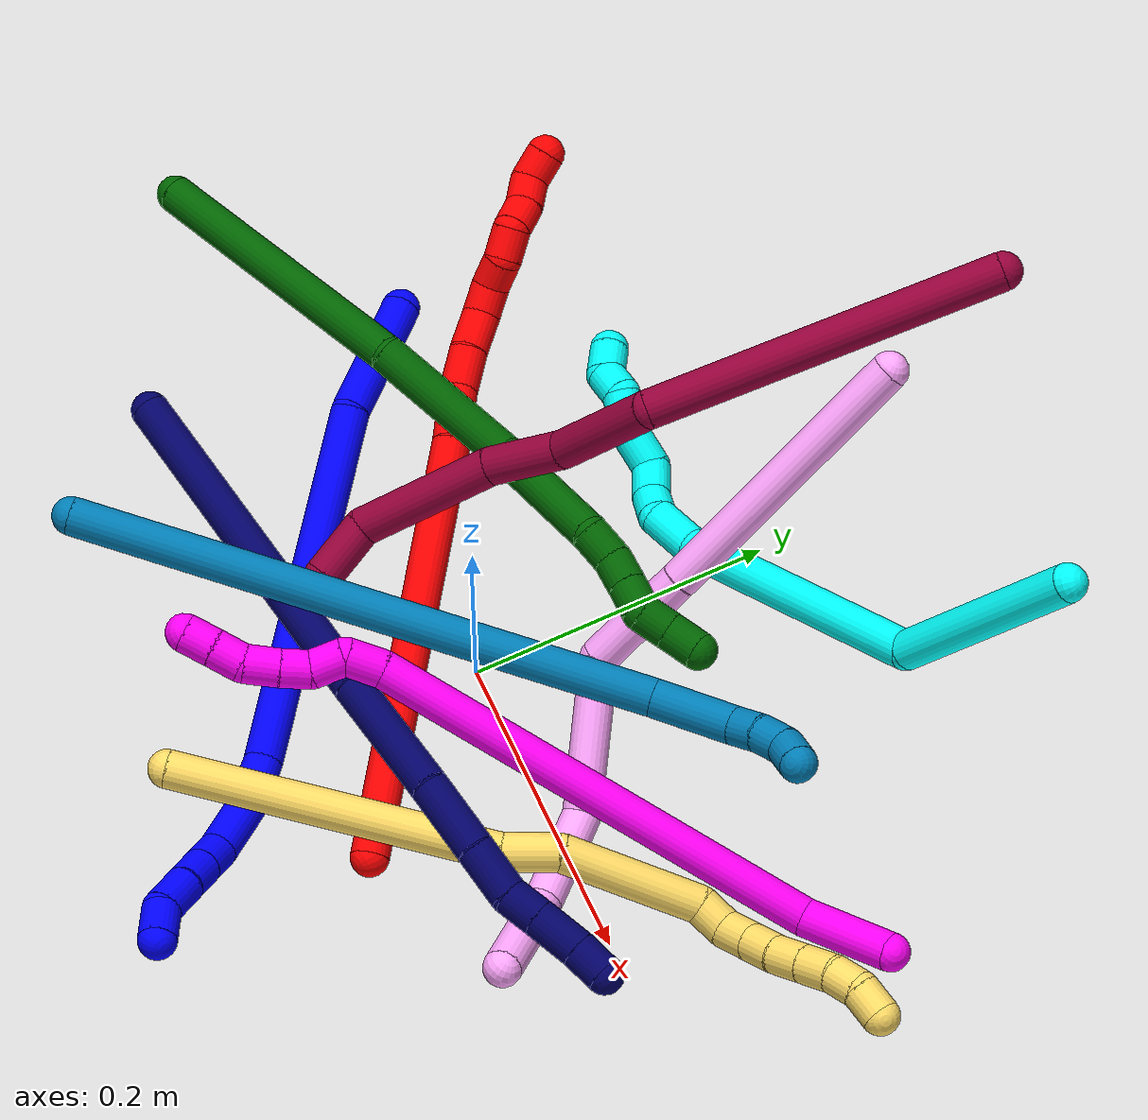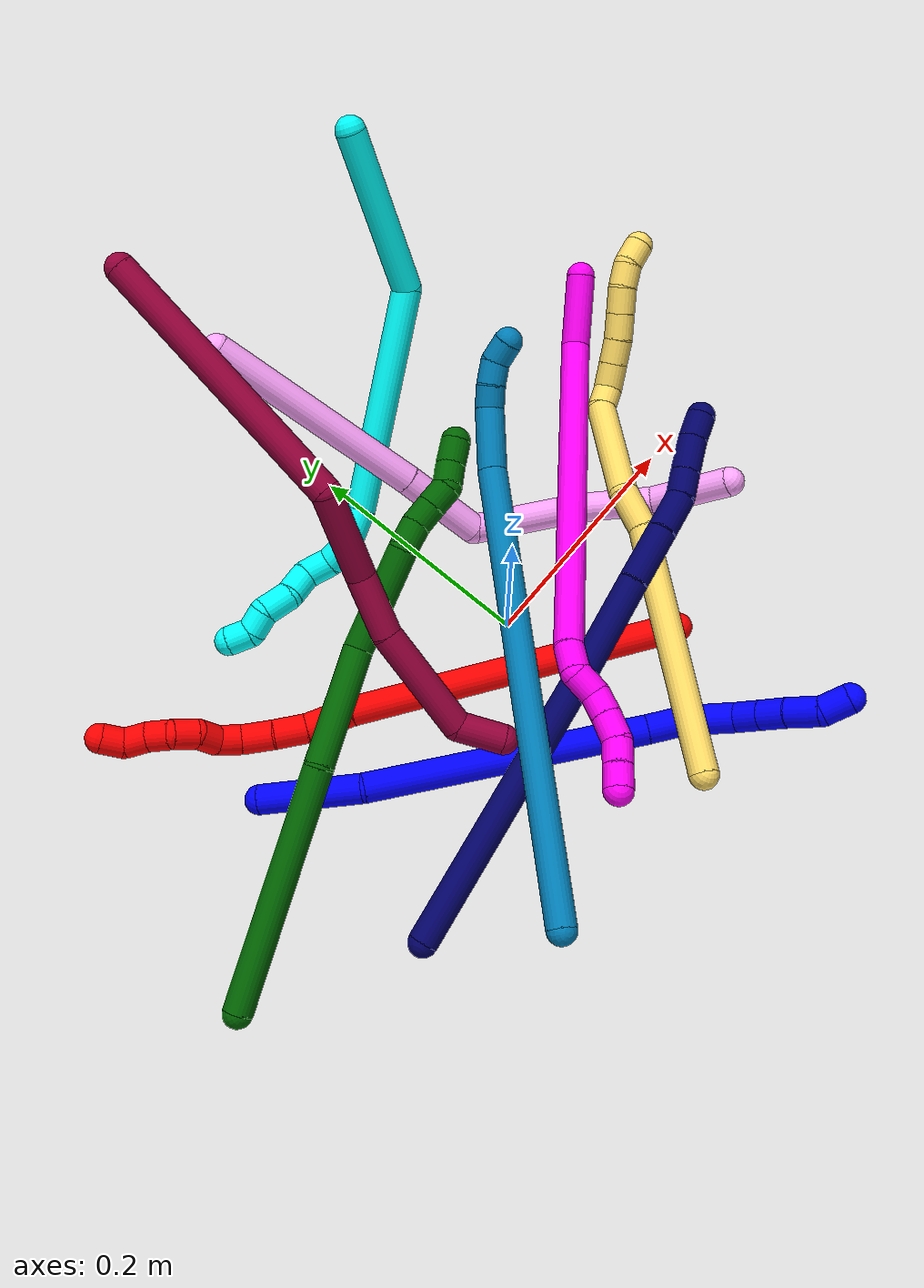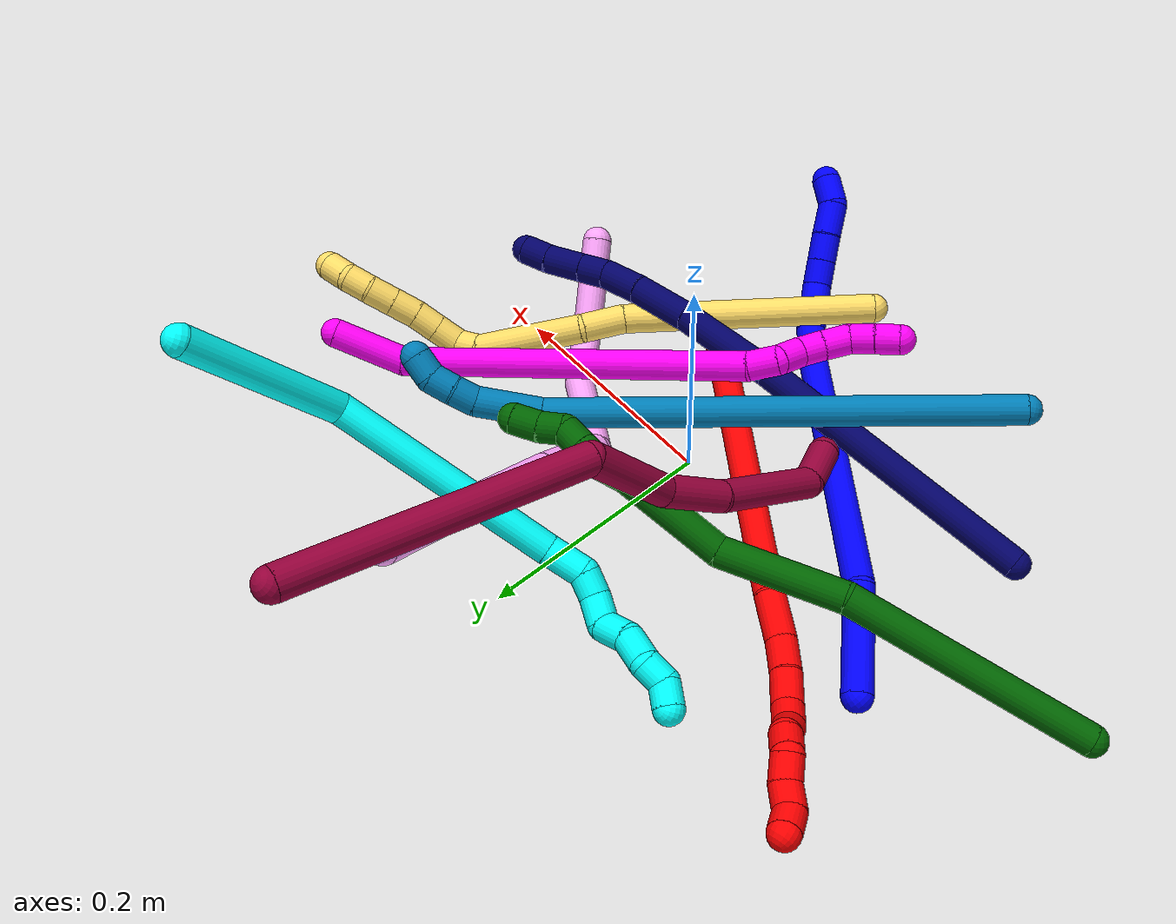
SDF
<sdf version="1.7">
 <world name="default">
  <plugin name="TubeGeneratorPlugin" filename="libtube_generator_plugin.so"/>
  <model name="photoneo_s_sensor">
   <static>1</static>
   <pose>0 0 2 1.57079 1.57079 3.14159</pose>
   <link name="link">
    <inertial><mass>0.1</mass></inertial>
    <sensor name="sensor" type="depth">
     <update_rate>30</update_rate>
     <camera>
      <horizontal_fov>1.22</horizontal_fov>
      <image><width>1920</width><height>1200</height><format>B8G8R8</format></image>
      <clip><near>0.1</near><far>4</far></clip>
      <depth_camera><output>points</output></depth_camera>
     </camera>
     <plugin name="camera_plugin" filename="libgazebo_ros_depth_camera.so">
      <baseline>0.2</baseline>
      <alwaysOn>1</alwaysOn>
      <updateRate>0.0</updateRate>
      <cameraName>camera_ir</cameraName>
      <imageTopicName>/camera/color/image_raw</imageTopicName>
      <cameraInfoTopicName>/camera/color/camera_info</cameraInfoTopicName>
      <depthImageTopicName>/camera/depth/image_raw</depthImageTopicName>
      <depthImageCameraInfoTopicName>/camera/depth/camera_info</depthImageCameraInfoTopicName>
      <pointCloudTopicName>/camera/depth/points</pointCloudTopicName>
      <frameName>fr_optical</frameName>
      <pointCloudCutoff>0.1</pointCloudCutoff>
      <pointCloudCutoffMax>2.0</pointCloudCutoffMax>
      <distortionK1>0</distortionK1>
      <distortionK2>0</distortionK2>
      <distortionK3>0</distortionK3>
      <distortionT1>0</distortionT1>
      <distortionT2>0</distortionT2>
      <CxPrime>0</CxPrime>
      <Cx>0</Cx>
      <Cy>0</Cy>
      <focalLength>0</focalLength>
      <hackBaseline>0</hackBaseline>
     </plugin>
    </sensor>
   </link>
  </model>
  <gravity>0 0 -9.8</gravity>
  <magnetic_field>6e-06 2.3e-05 -4.2e-05</magnetic_field>
  <atmosphere type="adiabatic"/>
  <physics name="default_physics" default="0" type="ode">
   <max_step_size>0.003</max_step_size>
   <real_time_factor>1</real_time_factor>
   <real_time_update_rate>1000</real_time_update_rate>
   <max_contacts>10000</max_contacts>
   <ode>
    <solver>
     <type>quick</type>
     <iters>100</iters>
     <sor>1.3</sor>
     <use_dynamic_moi_rescaling>0</use_dynamic_moi_rescaling>
    </solver>
    <constraints>
     <contact_max_correcting_vel>0</contact_max_correcting_vel>
     <contact_surface_layer>0.001</contact_surface_layer>
     <cfm>0</cfm>
     <erp>0.2</erp>
    </constraints>
   </ode>
  </physics>
  <scene><ambient>0.4 0.4 0.4 1</ambient><background>0.7 0.7 0.7 1</background><shadows>0</shadows></scene>
  <audio><device>default</device></audio>
  <spherical_coordinates>
   <surface_model>EARTH_WGS84</surface_model>
   <latitude_deg>0</latitude_deg>
   <longitude_deg>0</longitude_deg>
   <elevation>0</elevation>
   <heading_deg>0</heading_deg>
  </spherical_coordinates>
  <model name="bin">
   <static>1</static>
   <link name="bottom">
    <collision name="collision-bottom">
     <pose>0 0 -0.01 0 -0 0</pose>
     <geometry><box><size>0.8 0.6 0.02</size></box></geometry>
     <surface>
      <friction><ode><mu>100</mu><mu2>100</mu2></ode></friction>
      <contact><collide_bitmask>65535</collide_bitmask></contact>
     </surface>
    </collision>
   </link>
   <link name="west_wall">
    <collision name="collision-west_wall">
     <pose>-0.41 0 0.1 0 -0 0</pose>
     <geometry><box><size>0.02 0.6 0.2</size></box></geometry>
     <surface>
      <friction><ode><mu>100</mu><mu2>100</mu2></ode></friction>
      <contact><collide_bitmask>65535</collide_bitmask></contact>
     </surface>
    </collision>
   </link>
   <link name="east_wall">
    <collision name="collision-east_wall">
     <pose>0.41 0 0.1 0 -0 0</pose>
     <geometry><box><size>0.02 0.6 0.2</size></box></geometry>
     <surface>
      <friction><ode><mu>100</mu><mu2>100</mu2></ode></friction>
      <contact><collide_bitmask>65535</collide_bitmask></contact>
     </surface>
    </collision>
   </link>
   <link name="south_wall">
    <collision name="collision-south_wall">
     <pose>0 -0.31 0.1 0 -0 0</pose>
     <geometry><box><size>0.8 0.02 0.2</size></box></geometry>
     <surface>
      <friction><ode><mu>100</mu><mu2>100</mu2></ode></friction>
      <contact><collide_bitmask>65535</collide_bitmask></contact>
     </surface>
    </collision>
   </link>
   <link name="north_wall">
    <collision name="collision-north_wall">
     <pose>0 0.31 0.1 0 -0 0</pose>
     <geometry><box><size>0.8 0.02 0.2</size></box></geometry>
     <surface>
      <friction><ode><mu>100</mu><mu2>100</mu2></ode></friction>
      <contact><collide_bitmask>65535</collide_bitmask></contact>
     </surface>
    </collision>
   </link>
  </model>
  <model name="1">
   <static>0</static>
   <link name="1">
    <collision name="collision-cylinder-e_1_1_4">
     <pose>0.017141 -0.032568 0.02341 0.947561 0.403867 0.209171</pose>
     <geometry><cylinder><radius>0.0125</radius><length>0.087235</length></cylinder></geometry>
     <surface>
      <friction><ode><mu>1.16</mu><mu2>1.16</mu2><slip1>0</slip1><slip2>0</slip2></ode></friction>
      <contact><ode><kp>1e+06</kp><kd>1</kd><max_vel>0</max_vel><min_depth>0.001</min_depth></ode></contact>
     </surface>
    </collision>
    <visual name="visual-cylinder-e_1_1_4">
     <pose>0.017141 -0.032568 0.02341 0.947561 0.403867 0.209171</pose>
     <geometry><cylinder><radius>0.0125</radius><length>0.087235</length></cylinder></geometry>
     <material><ambient>0 0 1 1</ambient></material>
    </visual>
    <collision name="collision-cylinder-e_2_4_5">
     <pose>0.110646 -0.135112 0.107165 0.859164 0.690654 0.32667</pose>
     <geometry><cylinder><radius>0.0125</radius><length>0.239749</length></cylinder></geometry>
     <surface>
      <friction><ode><mu>1.16</mu><mu2>1.16</mu2><slip1>0</slip1><slip2>0</slip2></ode></friction>
      <contact><ode><kp>1e+06</kp><kd>1</kd><max_vel>0</max_vel><min_depth>0.001</min_depth></ode></contact>
     </surface>
    </collision>
    <visual name="visual-cylinder-e_2_4_5">
     <pose>0.110646 -0.135112 0.107165 0.859164 0.690654 0.32667</pose>
     <geometry><cylinder><radius>0.0125</radius><length>0.239749</length></cylinder></geometry>
     <material><ambient>0 0 1 1</ambient></material>
    </visual>
    <collision name="collision-cylinder-e_3_5_6">
     <pose>0.192903 -0.216041 0.177827 0.815344 0.373192 0.162706</pose>
     <geometry><cylinder><radius>0.0125</radius><length>0.032317</length></cylinder></geometry>
     <surface>
      <friction><ode><mu>1.16</mu><mu2>1.16</mu2><slip1>0</slip1><slip2>0</slip2></ode></friction>
      <contact><ode><kp>1e+06</kp><kd>1</kd><max_vel>0</max_vel><min_depth>0.001</min_depth></ode></contact>
     </surface>
    </collision>
    <visual name="visual-cylinder-e_3_5_6">
     <pose>0.192903 -0.216041 0.177827 0.815344 0.373192 0.162706</pose>
     <geometry><cylinder><radius>0.0125</radius><length>0.032317</length></cylinder></geometry>
     <material><ambient>0 0 1 1</ambient></material>
    </visual>
    <collision name="collision-cylinder-e_4_6_7">
     <pose>0.203812 -0.244161 0.199421 0.989507 0.239616 0.129715</pose>
     <geometry><cylinder><radius>0.0125</radius><length>0.042287</length></cylinder></geometry>
     <surface>
      <friction><ode><mu>1.16</mu><mu2>1.16</mu2><slip1>0</slip1><slip2>0</slip2></ode></friction>
      <contact><ode><kp>1e+06</kp><kd>1</kd><max_vel>0</max_vel><min_depth>0.001</min_depth></ode></contact>
     </surface>
    </collision>
    <visual name="visual-cylinder-e_4_6_7">
     <pose>0.203812 -0.244161 0.199421 0.989507 0.239616 0.129715</pose>
     <geometry><cylinder><radius>0.0125</radius><length>0.042287</length></cylinder></geometry>
     <material><ambient>0 0 1 1</ambient></material>
    </visual>
    <collision name="collision-cylinder-e_5_7_8">
     <pose>0.208047 -0.270223 0.217338 0.929741 -0.070385 -0.035311</pose>
     <geometry><cylinder><radius>0.0125</radius><length>0.022254</length></cylinder></geometry>
     <surface>
      <friction><ode><mu>1.16</mu><mu2>1.16</mu2><slip1>0</slip1><slip2>0</slip2></ode></friction>
      <contact><ode><kp>1e+06</kp><kd>1</kd><max_vel>0</max_vel><min_depth>0.001</min_depth></ode></contact>
     </surface>
    </collision>
    <visual name="visual-cylinder-e_5_7_8">
     <pose>0.208047 -0.270223 0.217338 0.929741 -0.070385 -0.035311</pose>
     <geometry><cylinder><radius>0.0125</radius><length>0.022254</length></cylinder></geometry>
     <material><ambient>0 0 1 1</ambient></material>
    </visual>
    <collision name="collision-cylinder-e_6_8_9">
     <pose>0.206502 -0.288426 0.230889 0.931917 -0.065699 -0.033049</pose>
     <geometry><cylinder><radius>0.0125</radius><length>0.023239</length></cylinder></geometry>
     <surface>
      <friction><ode><mu>1.16</mu><mu2>1.16</mu2><slip1>0</slip1><slip2>0</slip2></ode></friction>
      <contact><ode><kp>1e+06</kp><kd>1</kd><max_vel>0</max_vel><min_depth>0.001</min_depth></ode></contact>
     </surface>
    </collision>
    <visual name="visual-cylinder-e_6_8_9">
     <pose>0.206502 -0.288426 0.230889 0.931917 -0.065699 -0.033049</pose>
     <geometry><cylinder><radius>0.0125</radius><length>0.023239</length></cylinder></geometry>
     <material><ambient>0 0 1 1</ambient></material>
    </visual>
    <collision name="collision-cylinder-e_7_9_10">
     <pose>0.205889 -0.309697 0.245711 0.986689 0.01044 0.005614</pose>
     <geometry><cylinder><radius>0.0125</radius><length>0.028682</length></cylinder></geometry>
     <surface>
      <friction><ode><mu>1.16</mu><mu2>1.16</mu2><slip1>0</slip1><slip2>0</slip2></ode></friction>
      <contact><ode><kp>1e+06</kp><kd>1</kd><max_vel>0</max_vel><min_depth>0.001</min_depth></ode></contact>
     </surface>
    </collision>
    <visual name="visual-cylinder-e_7_9_10">
     <pose>0.205889 -0.309697 0.245711 0.986689 0.01044 0.005614</pose>
     <geometry><cylinder><radius>0.0125</radius><length>0.028682</length></cylinder></geometry>
     <material><ambient>0 0 1 1</ambient></material>
    </visual>
    <collision name="collision-cylinder-e_8_10_2">
     <pose>0.209588 -0.328269 0.263135 0.607081 0.297231 0.093721</pose>
     <geometry><cylinder><radius>0.0125</radius><length>0.024236</length></cylinder></geometry>
     <surface>
      <friction><ode><mu>1.16</mu><mu2>1.16</mu2><slip1>0</slip1><slip2>0</slip2></ode></friction>
      <contact><ode><kp>1e+06</kp><kd>1</kd><max_vel>0</max_vel><min_depth>0.001</min_depth></ode></contact>
     </surface>
    </collision>
    <visual name="visual-cylinder-e_8_10_2">
     <pose>0.209588 -0.328269 0.263135 0.607081 0.297231 0.093721</pose>
     <geometry><cylinder><radius>0.0125</radius><length>0.024236</length></cylinder></geometry>
     <material><ambient>0 0 1 1</ambient></material>
    </visual>
    <collision name="collision-sphere-2">
     <pose>0.213137 -0.334879 0.272652 0 -0 0</pose>
     <geometry><sphere><radius>0.0125</radius></sphere></geometry>
     <surface>
      <friction><ode><mu>1.16</mu><mu2>1.16</mu2><slip1>0</slip1><slip2>0</slip2></ode></friction>
      <contact><ode><kp>1e+06</kp><kd>1</kd><max_vel>0</max_vel><min_depth>0.001</min_depth></ode></contact>
     </surface>
    </collision>
    <visual name="visual-sphere-2">
     <pose>0.213137 -0.334879 0.272652 0 -0 0</pose>
     <geometry><sphere><radius>0.0125</radius></sphere></geometry>
     <material><ambient>0 0 1 1</ambient></material>
    </visual>
    <collision name="collision-sphere-10">
     <pose>0.206039 -0.321659 0.253619 0 -0 0</pose>
     <geometry><sphere><radius>0.0125</radius></sphere></geometry>
     <surface>
      <friction><ode><mu>1.16</mu><mu2>1.16</mu2><slip1>0</slip1><slip2>0</slip2></ode></friction>
      <contact><ode><kp>1e+06</kp><kd>1</kd><max_vel>0</max_vel><min_depth>0.001</min_depth></ode></contact>
     </surface>
    </collision>
    <visual name="visual-sphere-10">
     <pose>0.206039 -0.321659 0.253619 0 -0 0</pose>
     <geometry><sphere><radius>0.0125</radius></sphere></geometry>
     <material><ambient>0 0 1 1</ambient></material>
    </visual>
    <collision name="collision-sphere-9">
     <pose>0.205739 -0.297734 0.237803 0 -0 0</pose>
     <geometry><sphere><radius>0.0125</radius></sphere></geometry>
     <surface>
      <friction><ode><mu>1.16</mu><mu2>1.16</mu2><slip1>0</slip1><slip2>0</slip2></ode></friction>
      <contact><ode><kp>1e+06</kp><kd>1</kd><max_vel>0</max_vel><min_depth>0.001</min_depth></ode></contact>
     </surface>
    </collision>
    <visual name="visual-sphere-9">
     <pose>0.205739 -0.297734 0.237803 0 -0 0</pose>
     <geometry><sphere><radius>0.0125</radius></sphere></geometry>
     <material><ambient>0 0 1 1</ambient></material>
    </visual>
    <collision name="collision-sphere-4">
     <pose>0.034281 -0.065136 0.04682 0 -0 0</pose>
     <geometry><sphere><radius>0.0125</radius></sphere></geometry>
     <surface>
      <friction><ode><mu>1.16</mu><mu2>1.16</mu2><slip1>0</slip1><slip2>0</slip2></ode></friction>
      <contact><ode><kp>1e+06</kp><kd>1</kd><max_vel>0</max_vel><min_depth>0.001</min_depth></ode></contact>
     </surface>
    </collision>
    <visual name="visual-sphere-4">
     <pose>0.034281 -0.065136 0.04682 0 -0 0</pose>
     <geometry><sphere><radius>0.0125</radius></sphere></geometry>
     <material><ambient>0 0 1 1</ambient></material>
    </visual>
    <collision name="collision-sphere-1">
     <geometry><sphere><radius>0.0125</radius></sphere></geometry>
     <surface>
      <friction><ode><mu>1.16</mu><mu2>1.16</mu2><slip1>0</slip1><slip2>0</slip2></ode></friction>
      <contact><ode><kp>1e+06</kp><kd>1</kd><max_vel>0</max_vel><min_depth>0.001</min_depth></ode></contact>
     </surface>
    </collision>
    <visual name="visual-sphere-1">
     <geometry><sphere><radius>0.0125</radius></sphere></geometry>
     <material><ambient>0 0 1 1</ambient></material>
    </visual>
    <collision name="collision-sphere-8">
     <pose>0.207265 -0.279119 0.223976 0 -0 0</pose>
     <geometry><sphere><radius>0.0125</radius></sphere></geometry>
     <surface>
      <friction><ode><mu>1.16</mu><mu2>1.16</mu2><slip1>0</slip1><slip2>0</slip2></ode></friction>
      <contact><ode><kp>1e+06</kp><kd>1</kd><max_vel>0</max_vel><min_depth>0.001</min_depth></ode></contact>
     </surface>
    </collision>
    <visual name="visual-sphere-8">
     <pose>0.207265 -0.279119 0.223976 0 -0 0</pose>
     <geometry><sphere><radius>0.0125</radius></sphere></geometry>
     <material><ambient>0 0 1 1</ambient></material>
    </visual>
    <collision name="collision-sphere-5">
     <pose>0.187011 -0.205088 0.167511 0 -0 0</pose>
     <geometry><sphere><radius>0.0125</radius></sphere></geometry>
     <surface>
      <friction><ode><mu>1.16</mu><mu2>1.16</mu2><slip1>0</slip1><slip2>0</slip2></ode></friction>
      <contact><ode><kp>1e+06</kp><kd>1</kd><max_vel>0</max_vel><min_depth>0.001</min_depth></ode></contact>
     </surface>
    </collision>
    <visual name="visual-sphere-5">
     <pose>0.187011 -0.205088 0.167511 0 -0 0</pose>
     <geometry><sphere><radius>0.0125</radius></sphere></geometry>
     <material><ambient>0 0 1 1</ambient></material>
    </visual>
    <collision name="collision-sphere-6">
     <pose>0.198794 -0.226995 0.188143 0 -0 0</pose>
     <geometry><sphere><radius>0.0125</radius></sphere></geometry>
     <surface>
      <friction><ode><mu>1.16</mu><mu2>1.16</mu2><slip1>0</slip1><slip2>0</slip2></ode></friction>
      <contact><ode><kp>1e+06</kp><kd>1</kd><max_vel>0</max_vel><min_depth>0.001</min_depth></ode></contact>
     </surface>
    </collision>
    <visual name="visual-sphere-6">
     <pose>0.198794 -0.226995 0.188143 0 -0 0</pose>
     <geometry><sphere><radius>0.0125</radius></sphere></geometry>
     <material><ambient>0 0 1 1</ambient></material>
    </visual>
    <collision name="collision-sphere-7">
     <pose>0.20883 -0.261327 0.2107 0 -0 0</pose>
     <geometry><sphere><radius>0.0125</radius></sphere></geometry>
     <surface>
      <friction><ode><mu>1.16</mu><mu2>1.16</mu2><slip1>0</slip1><slip2>0</slip2></ode></friction>
      <contact><ode><kp>1e+06</kp><kd>1</kd><max_vel>0</max_vel><min_depth>0.001</min_depth></ode></contact>
     </surface>
    </collision>
    <visual name="visual-sphere-7">
     <pose>0.20883 -0.261327 0.2107 0 -0 0</pose>
     <geometry><sphere><radius>0.0125</radius></sphere></geometry>
     <material><ambient>0 0 1 1</ambient></material>
    </visual>
    <inertial>
     <pose>0.126578 -0.164192 0.131084 0 -0 0</pose>
     <mass>0.5</mass>
     <inertia><ixx>0.001234</ixx><ixy>0</ixy><ixz>0</ixz><iyy>0.001219</iyy><iyz>0</iyz><izz>-7e-06</izz></inertia>
    </inertial>
   </link>
   <pose>-0.246997 0.058526 0.011498 -0.453792 0.909827 -0.344468</pose>
  </model>
  <model name="2">
   <static>0</static>
   <link name="2">
    <collision name="collision-cylinder-e_1_1_4">
     <pose>-0.052506 0.084655 0.100923 -0.697958 -0.379301 0.139469</pose>
     <geometry><cylinder><radius>0.0125</radius><length>0.283611</length></cylinder></geometry>
     <surface>
      <friction><ode><mu>1.16</mu><mu2>1.16</mu2><slip1>0</slip1><slip2>0</slip2></ode></friction>
      <contact><ode><kp>1e+06</kp><kd>1</kd><max_vel>0</max_vel><min_depth>0.001</min_depth></ode></contact>
     </surface>
    </collision>
    <visual name="visual-cylinder-e_1_1_4">
     <pose>-0.052506 0.084655 0.100923 -0.697958 -0.379301 0.139469</pose>
     <geometry><cylinder><radius>0.0125</radius><length>0.283611</length></cylinder></geometry>
     <material><ambient>1 0 0 1</ambient></material>
    </visual>
    <collision name="collision-cylinder-e_2_4_5">
     <pose>-0.10929 0.182686 0.215459 -0.776657 -0.22044 0.090488</pose>
     <geometry><cylinder><radius>0.0125</radius><length>0.039117</length></cylinder></geometry>
     <surface>
      <friction><ode><mu>1.16</mu><mu2>1.16</mu2><slip1>0</slip1><slip2>0</slip2></ode></friction>
      <contact><ode><kp>1e+06</kp><kd>1</kd><max_vel>0</max_vel><min_depth>0.001</min_depth></ode></contact>
     </surface>
    </collision>
    <visual name="visual-cylinder-e_2_4_5">
     <pose>-0.10929 0.182686 0.215459 -0.776657 -0.22044 0.090488</pose>
     <geometry><cylinder><radius>0.0125</radius><length>0.039117</length></cylinder></geometry>
     <material><ambient>1 0 0 1</ambient></material>
    </visual>
    <collision name="collision-cylinder-e_3_5_6">
     <pose>-0.119309 0.203674 0.239362 -0.63682 -0.421775 0.140893</pose>
     <geometry><cylinder><radius>0.0125</radius><length>0.028057</length></cylinder></geometry>
     <surface>
      <friction><ode><mu>1.16</mu><mu2>1.16</mu2><slip1>0</slip1><slip2>0</slip2></ode></friction>
      <contact><ode><kp>1e+06</kp><kd>1</kd><max_vel>0</max_vel><min_depth>0.001</min_depth></ode></contact>
     </surface>
    </collision>
    <visual name="visual-cylinder-e_3_5_6">
     <pose>-0.119309 0.203674 0.239362 -0.63682 -0.421775 0.140893</pose>
     <geometry><cylinder><radius>0.0125</radius><length>0.028057</length></cylinder></geometry>
     <material><ambient>1 0 0 1</ambient></material>
    </visual>
    <collision name="collision-cylinder-e_4_6_7">
     <pose>-0.129032 0.218369 0.260696 -0.570383 -0.294505 0.086919</pose>
     <geometry><cylinder><radius>0.0125</radius><length>0.027421</length></cylinder></geometry>
     <surface>
      <friction><ode><mu>1.16</mu><mu2>1.16</mu2><slip1>0</slip1><slip2>0</slip2></ode></friction>
      <contact><ode><kp>1e+06</kp><kd>1</kd><max_vel>0</max_vel><min_depth>0.001</min_depth></ode></contact>
     </surface>
    </collision>
    <visual name="visual-cylinder-e_4_6_7">
     <pose>-0.129032 0.218369 0.260696 -0.570383 -0.294505 0.086919</pose>
     <geometry><cylinder><radius>0.0125</radius><length>0.027421</length></cylinder></geometry>
     <material><ambient>1 0 0 1</ambient></material>
    </visual>
    <collision name="collision-cylinder-e_5_7_8">
     <pose>-0.139715 0.229131 0.278696 -0.486231 -0.705527 0.18212</pose>
     <geometry><cylinder><radius>0.0125</radius><length>0.020673</length></cylinder></geometry>
     <surface>
      <friction><ode><mu>1.16</mu><mu2>1.16</mu2><slip1>0</slip1><slip2>0</slip2></ode></friction>
      <contact><ode><kp>1e+06</kp><kd>1</kd><max_vel>0</max_vel><min_depth>0.001</min_depth></ode></contact>
     </surface>
    </collision>
    <visual name="visual-cylinder-e_5_7_8">
     <pose>-0.139715 0.229131 0.278696 -0.486231 -0.705527 0.18212</pose>
     <geometry><cylinder><radius>0.0125</radius><length>0.020673</length></cylinder></geometry>
     <material><ambient>1 0 0 1</ambient></material>
    </visual>
    <collision name="collision-cylinder-e_6_8_9">
     <pose>-0.155284 0.232697 0.290351 0.023553 -1.08344 -0.014174</pose>
     <geometry><cylinder><radius>0.0125</radius><length>0.02007</length></cylinder></geometry>
     <surface>
      <friction><ode><mu>1.16</mu><mu2>1.16</mu2><slip1>0</slip1><slip2>0</slip2></ode></friction>
      <contact><ode><kp>1e+06</kp><kd>1</kd><max_vel>0</max_vel><min_depth>0.001</min_depth></ode></contact>
     </surface>
    </collision>
    <visual name="visual-cylinder-e_6_8_9">
     <pose>-0.155284 0.232697 0.290351 0.023553 -1.08344 -0.014174</pose>
     <geometry><cylinder><radius>0.0125</radius><length>0.02007</length></cylinder></geometry>
     <material><ambient>1 0 0 1</ambient></material>
    </visual>
    <collision name="collision-cylinder-e_7_9_10">
     <pose>-0.171144 0.236239 0.301741 -0.499612 -0.742263 0.197931</pose>
     <geometry><cylinder><radius>0.0125</radius><length>0.02069</length></cylinder></geometry>
     <surface>
      <friction><ode><mu>1.16</mu><mu2>1.16</mu2><slip1>0</slip1><slip2>0</slip2></ode></friction>
      <contact><ode><kp>1e+06</kp><kd>1</kd><max_vel>0</max_vel><min_depth>0.001</min_depth></ode></contact>
     </surface>
    </collision>
    <visual name="visual-cylinder-e_7_9_10">
     <pose>-0.171144 0.236239 0.301741 -0.499612 -0.742263 0.197931</pose>
     <geometry><cylinder><radius>0.0125</radius><length>0.02069</length></cylinder></geometry>
     <material><ambient>1 0 0 1</ambient></material>
    </visual>
    <collision name="collision-cylinder-e_8_10_11">
     <pose>-0.179069 0.244579 0.317382 -0.482518 -0.092089 0.022674</pose>
     <geometry><cylinder><radius>0.0125</radius><length>0.02029</length></cylinder></geometry>
     <surface>
      <friction><ode><mu>1.16</mu><mu2>1.16</mu2><slip1>0</slip1><slip2>0</slip2></ode></friction>
      <contact><ode><kp>1e+06</kp><kd>1</kd><max_vel>0</max_vel><min_depth>0.001</min_depth></ode></contact>
     </surface>
    </collision>
    <visual name="visual-cylinder-e_8_10_11">
     <pose>-0.179069 0.244579 0.317382 -0.482518 -0.092089 0.022674</pose>
     <geometry><cylinder><radius>0.0125</radius><length>0.02029</length></cylinder></geometry>
     <material><ambient>1 0 0 1</ambient></material>
    </visual>
    <collision name="collision-cylinder-e_9_11_12">
     <pose>-0.182935 0.255415 0.333664 -0.697688 -0.297322 0.108838</pose>
     <geometry><cylinder><radius>0.0125</radius><length>0.020018</length></cylinder></geometry>
     <surface>
      <friction><ode><mu>1.16</mu><mu2>1.16</mu2><slip1>0</slip1><slip2>0</slip2></ode></friction>
      <contact><ode><kp>1e+06</kp><kd>1</kd><max_vel>0</max_vel><min_depth>0.001</min_depth></ode></contact>
     </surface>
    </collision>
    <visual name="visual-cylinder-e_9_11_12">
     <pose>-0.182935 0.255415 0.333664 -0.697688 -0.297322 0.108838</pose>
     <geometry><cylinder><radius>0.0125</radius><length>0.020018</length></cylinder></geometry>
     <material><ambient>1 0 0 1</ambient></material>
    </visual>
    <collision name="collision-cylinder-e_10_12_2">
     <pose>-0.191838 0.263133 0.348897 -0.196208 -0.637966 0.064986</pose>
     <geometry><cylinder><radius>0.0125</radius><length>0.020051</length></cylinder></geometry>
     <surface>
      <friction><ode><mu>1.16</mu><mu2>1.16</mu2><slip1>0</slip1><slip2>0</slip2></ode></friction>
      <contact><ode><kp>1e+06</kp><kd>1</kd><max_vel>0</max_vel><min_depth>0.001</min_depth></ode></contact>
     </surface>
    </collision>
    <visual name="visual-cylinder-e_10_12_2">
     <pose>-0.191838 0.263133 0.348897 -0.196208 -0.637966 0.064986</pose>
     <geometry><cylinder><radius>0.0125</radius><length>0.020051</length></cylinder></geometry>
     <material><ambient>1 0 0 1</ambient></material>
    </visual>
    <collision name="collision-sphere-2">
     <pose>-0.197809 0.264703 0.356796 0 -0 0</pose>
     <geometry><sphere><radius>0.0125</radius></sphere></geometry>
     <surface>
      <friction><ode><mu>1.16</mu><mu2>1.16</mu2><slip1>0</slip1><slip2>0</slip2></ode></friction>
      <contact><ode><kp>1e+06</kp><kd>1</kd><max_vel>0</max_vel><min_depth>0.001</min_depth></ode></contact>
     </surface>
    </collision>
    <visual name="visual-sphere-2">
     <pose>-0.197809 0.264703 0.356796 0 -0 0</pose>
     <geometry><sphere><radius>0.0125</radius></sphere></geometry>
     <material><ambient>1 0 0 1</ambient></material>
    </visual>
    <collision name="collision-sphere-12">
     <pose>-0.185867 0.261563 0.340998 0 -0 0</pose>
     <geometry><sphere><radius>0.0125</radius></sphere></geometry>
     <surface>
      <friction><ode><mu>1.16</mu><mu2>1.16</mu2><slip1>0</slip1><slip2>0</slip2></ode></friction>
      <contact><ode><kp>1e+06</kp><kd>1</kd><max_vel>0</max_vel><min_depth>0.001</min_depth></ode></contact>
     </surface>
    </collision>
    <visual name="visual-sphere-12">
     <pose>-0.185867 0.261563 0.340998 0 -0 0</pose>
     <geometry><sphere><radius>0.0125</radius></sphere></geometry>
     <material><ambient>1 0 0 1</ambient></material>
    </visual>
    <collision name="collision-sphere-11">
     <pose>-0.180002 0.249267 0.32633 0 -0 0</pose>
     <geometry><sphere><radius>0.0125</radius></sphere></geometry>
     <surface>
      <friction><ode><mu>1.16</mu><mu2>1.16</mu2><slip1>0</slip1><slip2>0</slip2></ode></friction>
      <contact><ode><kp>1e+06</kp><kd>1</kd><max_vel>0</max_vel><min_depth>0.001</min_depth></ode></contact>
     </surface>
    </collision>
    <visual name="visual-sphere-11">
     <pose>-0.180002 0.249267 0.32633 0 -0 0</pose>
     <geometry><sphere><radius>0.0125</radius></sphere></geometry>
     <material><ambient>1 0 0 1</ambient></material>
    </visual>
    <collision name="collision-sphere-10">
     <pose>-0.178136 0.239892 0.308433 0 -0 0</pose>
     <geometry><sphere><radius>0.0125</radius></sphere></geometry>
     <surface>
      <friction><ode><mu>1.16</mu><mu2>1.16</mu2><slip1>0</slip1><slip2>0</slip2></ode></friction>
      <contact><ode><kp>1e+06</kp><kd>1</kd><max_vel>0</max_vel><min_depth>0.001</min_depth></ode></contact>
     </surface>
    </collision>
    <visual name="visual-sphere-10">
     <pose>-0.178136 0.239892 0.308433 0 -0 0</pose>
     <geometry><sphere><radius>0.0125</radius></sphere></geometry>
     <material><ambient>1 0 0 1</ambient></material>
    </visual>
    <collision name="collision-sphere-9">
     <pose>-0.164151 0.232587 0.295049 0 -0 0</pose>
     <geometry><sphere><radius>0.0125</radius></sphere></geometry>
     <surface>
      <friction><ode><mu>1.16</mu><mu2>1.16</mu2><slip1>0</slip1><slip2>0</slip2></ode></friction>
      <contact><ode><kp>1e+06</kp><kd>1</kd><max_vel>0</max_vel><min_depth>0.001</min_depth></ode></contact>
     </surface>
    </collision>
    <visual name="visual-sphere-9">
     <pose>-0.164151 0.232587 0.295049 0 -0 0</pose>
     <geometry><sphere><radius>0.0125</radius></sphere></geometry>
     <material><ambient>1 0 0 1</ambient></material>
    </visual>
    <collision name="collision-sphere-4">
     <pose>-0.105013 0.169309 0.201846 0 -0 0</pose>
     <geometry><sphere><radius>0.0125</radius></sphere></geometry>
     <surface>
      <friction><ode><mu>1.16</mu><mu2>1.16</mu2><slip1>0</slip1><slip2>0</slip2></ode></friction>
      <contact><ode><kp>1e+06</kp><kd>1</kd><max_vel>0</max_vel><min_depth>0.001</min_depth></ode></contact>
     </surface>
    </collision>
    <visual name="visual-sphere-4">
     <pose>-0.105013 0.169309 0.201846 0 -0 0</pose>
     <geometry><sphere><radius>0.0125</radius></sphere></geometry>
     <material><ambient>1 0 0 1</ambient></material>
    </visual>
    <collision name="collision-sphere-1">
     <geometry><sphere><radius>0.0125</radius></sphere></geometry>
     <surface>
      <friction><ode><mu>1.16</mu><mu2>1.16</mu2><slip1>0</slip1><slip2>0</slip2></ode></friction>
      <contact><ode><kp>1e+06</kp><kd>1</kd><max_vel>0</max_vel><min_depth>0.001</min_depth></ode></contact>
     </surface>
    </collision>
    <visual name="visual-sphere-1">
     <geometry><sphere><radius>0.0125</radius></sphere></geometry>
     <material><ambient>1 0 0 1</ambient></material>
    </visual>
    <collision name="collision-sphere-8">
     <pose>-0.146417 0.232808 0.285653 0 -0 0</pose>
     <geometry><sphere><radius>0.0125</radius></sphere></geometry>
     <surface>
      <friction><ode><mu>1.16</mu><mu2>1.16</mu2><slip1>0</slip1><slip2>0</slip2></ode></friction>
      <contact><ode><kp>1e+06</kp><kd>1</kd><max_vel>0</max_vel><min_depth>0.001</min_depth></ode></contact>
     </surface>
    </collision>
    <visual name="visual-sphere-8">
     <pose>-0.146417 0.232808 0.285653 0 -0 0</pose>
     <geometry><sphere><radius>0.0125</radius></sphere></geometry>
     <material><ambient>1 0 0 1</ambient></material>
    </visual>
    <collision name="collision-sphere-5">
     <pose>-0.113566 0.196063 0.229072 0 -0 0</pose>
     <geometry><sphere><radius>0.0125</radius></sphere></geometry>
     <surface>
      <friction><ode><mu>1.16</mu><mu2>1.16</mu2><slip1>0</slip1><slip2>0</slip2></ode></friction>
      <contact><ode><kp>1e+06</kp><kd>1</kd><max_vel>0</max_vel><min_depth>0.001</min_depth></ode></contact>
     </surface>
    </collision>
    <visual name="visual-sphere-5">
     <pose>-0.113566 0.196063 0.229072 0 -0 0</pose>
     <geometry><sphere><radius>0.0125</radius></sphere></geometry>
     <material><ambient>1 0 0 1</ambient></material>
    </visual>
    <collision name="collision-sphere-6">
     <pose>-0.125052 0.211285 0.249653 0 -0 0</pose>
     <geometry><sphere><radius>0.0125</radius></sphere></geometry>
     <surface>
      <friction><ode><mu>1.16</mu><mu2>1.16</mu2><slip1>0</slip1><slip2>0</slip2></ode></friction>
      <contact><ode><kp>1e+06</kp><kd>1</kd><max_vel>0</max_vel><min_depth>0.001</min_depth></ode></contact>
     </surface>
    </collision>
    <visual name="visual-sphere-6">
     <pose>-0.125052 0.211285 0.249653 0 -0 0</pose>
     <geometry><sphere><radius>0.0125</radius></sphere></geometry>
     <material><ambient>1 0 0 1</ambient></material>
    </visual>
    <collision name="collision-sphere-7">
     <pose>-0.133012 0.225454 0.271739 0 -0 0</pose>
     <geometry><sphere><radius>0.0125</radius></sphere></geometry>
     <surface>
      <friction><ode><mu>1.16</mu><mu2>1.16</mu2><slip1>0</slip1><slip2>0</slip2></ode></friction>
      <contact><ode><kp>1e+06</kp><kd>1</kd><max_vel>0</max_vel><min_depth>0.001</min_depth></ode></contact>
     </surface>
    </collision>
    <visual name="visual-sphere-7">
     <pose>-0.133012 0.225454 0.271739 0 -0 0</pose>
     <geometry><sphere><radius>0.0125</radius></sphere></geometry>
     <material><ambient>1 0 0 1</ambient></material>
    </visual>
    <inertial>
     <pose>-0.09348 0.145009 0.177725 0 -0 0</pose>
     <mass>0.5</mass>
     <inertia>
      <ixx>0.002011</ixx>
      <ixy>0</ixy>
      <ixz>0</ixz>
      <iyy>0.001801</iyy>
      <iyz>0</iyz>
      <izz>-0.000408</izz>
     </inertia>
    </inertial>
   </link>
   <pose>0.088509 -0.113567 0.011498 -2.31704 1.21077 -0.490082</pose>
  </model>
  <model name="3">
   <static>0</static>
   <link name="3">
    <collision name="collision-cylinder-e_1_1_4">
     <pose>0.008273 0.009005 -0.068783 -3.01141 0.118693 -1.47828</pose>
     <geometry><cylinder><radius>0.0125</radius><length>0.139723</length></cylinder></geometry>
     <surface>
      <friction><ode><mu>1.16</mu><mu2>1.16</mu2><slip1>0</slip1><slip2>0</slip2></ode></friction>
      <contact><ode><kp>1e+06</kp><kd>1</kd><max_vel>0</max_vel><min_depth>0.001</min_depth></ode></contact>
     </surface>
    </collision>
    <visual name="visual-cylinder-e_1_1_4">
     <pose>0.008273 0.009005 -0.068783 -3.01141 0.118693 -1.47828</pose>
     <geometry><cylinder><radius>0.0125</radius><length>0.139723</length></cylinder></geometry>
     <material><ambient>0.003922 1 0.996078 1</ambient></material>
    </visual>
    <collision name="collision-cylinder-e_2_4_5">
     <pose>-0.031273 0.033772 -0.21838 -2.94898 -0.526154 2.45278</pose>
     <geometry><cylinder><radius>0.0125</radius><length>0.190429</length></cylinder></geometry>
     <surface>
      <friction><ode><mu>1.16</mu><mu2>1.16</mu2><slip1>0</slip1><slip2>0</slip2></ode></friction>
      <contact><ode><kp>1e+06</kp><kd>1</kd><max_vel>0</max_vel><min_depth>0.001</min_depth></ode></contact>
     </surface>
    </collision>
    <visual name="visual-cylinder-e_2_4_5">
     <pose>-0.031273 0.033772 -0.21838 -2.94898 -0.526154 2.45278</pose>
     <geometry><cylinder><radius>0.0125</radius><length>0.190429</length></cylinder></geometry>
     <material><ambient>0.003922 1 0.996078 1</ambient></material>
    </visual>
    <collision name="collision-cylinder-e_3_5_6">
     <pose>-0.091221 0.050382 -0.310335 -3.06555 -0.826438 2.96851</pose>
     <geometry><cylinder><radius>0.0125</radius><length>0.032986</length></cylinder></geometry>
     <surface>
      <friction><ode><mu>1.16</mu><mu2>1.16</mu2><slip1>0</slip1><slip2>0</slip2></ode></friction>
      <contact><ode><kp>1e+06</kp><kd>1</kd><max_vel>0</max_vel><min_depth>0.001</min_depth></ode></contact>
     </surface>
    </collision>
    <visual name="visual-cylinder-e_3_5_6">
     <pose>-0.091221 0.050382 -0.310335 -3.06555 -0.826438 2.96851</pose>
     <geometry><cylinder><radius>0.0125</radius><length>0.032986</length></cylinder></geometry>
     <material><ambient>0.003922 1 0.996078 1</ambient></material>
    </visual>
    <collision name="collision-cylinder-e_4_6_7">
     <pose>-0.109922 0.057169 -0.326323 -2.25522 -0.708622 1.324</pose>
     <geometry><cylinder><radius>0.0125</radius><length>0.020191</length></cylinder></geometry>
     <surface>
      <friction><ode><mu>1.16</mu><mu2>1.16</mu2><slip1>0</slip1><slip2>0</slip2></ode></friction>
      <contact><ode><kp>1e+06</kp><kd>1</kd><max_vel>0</max_vel><min_depth>0.001</min_depth></ode></contact>
     </surface>
    </collision>
    <visual name="visual-cylinder-e_4_6_7">
     <pose>-0.109922 0.057169 -0.326323 -2.25522 -0.708622 1.324</pose>
     <geometry><cylinder><radius>0.0125</radius><length>0.020191</length></cylinder></geometry>
     <material><ambient>0.003922 1 0.996078 1</ambient></material>
    </visual>
    <collision name="collision-cylinder-e_5_7_8">
     <pose>-0.126498 0.069593 -0.333157 -1.8683 -0.975064 1.24429</pose>
     <geometry><cylinder><radius>0.0125</radius><length>0.024176</length></cylinder></geometry>
     <surface>
      <friction><ode><mu>1.16</mu><mu2>1.16</mu2><slip1>0</slip1><slip2>0</slip2></ode></friction>
      <contact><ode><kp>1e+06</kp><kd>1</kd><max_vel>0</max_vel><min_depth>0.001</min_depth></ode></contact>
     </surface>
    </collision>
    <visual name="visual-cylinder-e_5_7_8">
     <pose>-0.126498 0.069593 -0.333157 -1.8683 -0.975064 1.24429</pose>
     <geometry><cylinder><radius>0.0125</radius><length>0.024176</length></cylinder></geometry>
     <material><ambient>0.003922 1 0.996078 1</ambient></material>
    </visual>
    <collision name="collision-cylinder-e_6_8_9">
     <pose>-0.14864 0.073526 -0.33824 2.45206 -1.25162 -2.21928</pose>
     <geometry><cylinder><radius>0.0125</radius><length>0.025565</length></cylinder></geometry>
     <surface>
      <friction><ode><mu>1.16</mu><mu2>1.16</mu2><slip1>0</slip1><slip2>0</slip2></ode></friction>
      <contact><ode><kp>1e+06</kp><kd>1</kd><max_vel>0</max_vel><min_depth>0.001</min_depth></ode></contact>
     </surface>
    </collision>
    <visual name="visual-cylinder-e_6_8_9">
     <pose>-0.14864 0.073526 -0.33824 2.45206 -1.25162 -2.21928</pose>
     <geometry><cylinder><radius>0.0125</radius><length>0.025565</length></cylinder></geometry>
     <material><ambient>0.003922 1 0.996078 1</ambient></material>
    </visual>
    <collision name="collision-cylinder-e_7_9_10">
     <pose>-0.173504 0.073571 -0.342838 -2.09556 -1.33925 1.88262</pose>
     <geometry><cylinder><radius>0.0125</radius><length>0.026151</length></cylinder></geometry>
     <surface>
      <friction><ode><mu>1.16</mu><mu2>1.16</mu2><slip1>0</slip1><slip2>0</slip2></ode></friction>
      <contact><ode><kp>1e+06</kp><kd>1</kd><max_vel>0</max_vel><min_depth>0.001</min_depth></ode></contact>
     </surface>
    </collision>
    <visual name="visual-cylinder-e_7_9_10">
     <pose>-0.173504 0.073571 -0.342838 -2.09556 -1.33925 1.88262</pose>
     <geometry><cylinder><radius>0.0125</radius><length>0.026151</length></cylinder></geometry>
     <material><ambient>0.003922 1 0.996078 1</ambient></material>
    </visual>
    <collision name="collision-cylinder-e_8_10_11">
     <pose>-0.193824 0.078748 -0.350456 -2.74228 -0.852582 2.30327</pose>
     <geometry><cylinder><radius>0.0125</radius><length>0.02017</length></cylinder></geometry>
     <surface>
      <friction><ode><mu>1.16</mu><mu2>1.16</mu2><slip1>0</slip1><slip2>0</slip2></ode></friction>
      <contact><ode><kp>1e+06</kp><kd>1</kd><max_vel>0</max_vel><min_depth>0.001</min_depth></ode></contact>
     </surface>
    </collision>
    <visual name="visual-cylinder-e_8_10_11">
     <pose>-0.193824 0.078748 -0.350456 -2.74228 -0.852582 2.30327</pose>
     <geometry><cylinder><radius>0.0125</radius><length>0.02017</length></cylinder></geometry>
     <material><ambient>0.003922 1 0.996078 1</ambient></material>
    </visual>
    <collision name="collision-cylinder-e_9_11_2">
     <pose>-0.209474 0.087702 -0.357382 -1.6975 -0.89755 1.00073</pose>
     <geometry><cylinder><radius>0.0125</radius><length>0.02061</length></cylinder></geometry>
     <surface>
      <friction><ode><mu>1.16</mu><mu2>1.16</mu2><slip1>0</slip1><slip2>0</slip2></ode></friction>
      <contact><ode><kp>1e+06</kp><kd>1</kd><max_vel>0</max_vel><min_depth>0.001</min_depth></ode></contact>
     </surface>
    </collision>
    <visual name="visual-cylinder-e_9_11_2">
     <pose>-0.209474 0.087702 -0.357382 -1.6975 -0.89755 1.00073</pose>
     <geometry><cylinder><radius>0.0125</radius><length>0.02061</length></cylinder></geometry>
     <material><ambient>0.003922 1 0.996078 1</ambient></material>
    </visual>
    <collision name="collision-sphere-2">
     <pose>-0.21753 0.094076 -0.358194 0 -0 0</pose>
     <geometry><sphere><radius>0.0125</radius></sphere></geometry>
     <surface>
      <friction><ode><mu>1.16</mu><mu2>1.16</mu2><slip1>0</slip1><slip2>0</slip2></ode></friction>
      <contact><ode><kp>1e+06</kp><kd>1</kd><max_vel>0</max_vel><min_depth>0.001</min_depth></ode></contact>
     </surface>
    </collision>
    <visual name="visual-sphere-2">
     <pose>-0.21753 0.094076 -0.358194 0 -0 0</pose>
     <geometry><sphere><radius>0.0125</radius></sphere></geometry>
     <material><ambient>0.003922 1 0.996078 1</ambient></material>
    </visual>
    <collision name="collision-sphere-11">
     <pose>-0.201418 0.081328 -0.35657 0 -0 0</pose>
     <geometry><sphere><radius>0.0125</radius></sphere></geometry>
     <surface>
      <friction><ode><mu>1.16</mu><mu2>1.16</mu2><slip1>0</slip1><slip2>0</slip2></ode></friction>
      <contact><ode><kp>1e+06</kp><kd>1</kd><max_vel>0</max_vel><min_depth>0.001</min_depth></ode></contact>
     </surface>
    </collision>
    <visual name="visual-sphere-11">
     <pose>-0.201418 0.081328 -0.35657 0 -0 0</pose>
     <geometry><sphere><radius>0.0125</radius></sphere></geometry>
     <material><ambient>0.003922 1 0.996078 1</ambient></material>
    </visual>
    <collision name="collision-sphere-10">
     <pose>-0.18623 0.076168 -0.344341 0 -0 0</pose>
     <geometry><sphere><radius>0.0125</radius></sphere></geometry>
     <surface>
      <friction><ode><mu>1.16</mu><mu2>1.16</mu2><slip1>0</slip1><slip2>0</slip2></ode></friction>
      <contact><ode><kp>1e+06</kp><kd>1</kd><max_vel>0</max_vel><min_depth>0.001</min_depth></ode></contact>
     </surface>
    </collision>
    <visual name="visual-sphere-10">
     <pose>-0.18623 0.076168 -0.344341 0 -0 0</pose>
     <geometry><sphere><radius>0.0125</radius></sphere></geometry>
     <material><ambient>0.003922 1 0.996078 1</ambient></material>
    </visual>
    <collision name="collision-sphere-9">
     <pose>-0.160777 0.070974 -0.341335 0 -0 0</pose>
     <geometry><sphere><radius>0.0125</radius></sphere></geometry>
     <surface>
      <friction><ode><mu>1.16</mu><mu2>1.16</mu2><slip1>0</slip1><slip2>0</slip2></ode></friction>
      <contact><ode><kp>1e+06</kp><kd>1</kd><max_vel>0</max_vel><min_depth>0.001</min_depth></ode></contact>
     </surface>
    </collision>
    <visual name="visual-sphere-9">
     <pose>-0.160777 0.070974 -0.341335 0 -0 0</pose>
     <geometry><sphere><radius>0.0125</radius></sphere></geometry>
     <material><ambient>0.003922 1 0.996078 1</ambient></material>
    </visual>
    <collision name="collision-sphere-4">
     <pose>0.016545 0.018011 -0.137566 0 -0 0</pose>
     <geometry><sphere><radius>0.0125</radius></sphere></geometry>
     <surface>
      <friction><ode><mu>1.16</mu><mu2>1.16</mu2><slip1>0</slip1><slip2>0</slip2></ode></friction>
      <contact><ode><kp>1e+06</kp><kd>1</kd><max_vel>0</max_vel><min_depth>0.001</min_depth></ode></contact>
     </surface>
    </collision>
    <visual name="visual-sphere-4">
     <pose>0.016545 0.018011 -0.137566 0 -0 0</pose>
     <geometry><sphere><radius>0.0125</radius></sphere></geometry>
     <material><ambient>0.003922 1 0.996078 1</ambient></material>
    </visual>
    <collision name="collision-sphere-1">
     <geometry><sphere><radius>0.0125</radius></sphere></geometry>
     <surface>
      <friction><ode><mu>1.16</mu><mu2>1.16</mu2><slip1>0</slip1><slip2>0</slip2></ode></friction>
      <contact><ode><kp>1e+06</kp><kd>1</kd><max_vel>0</max_vel><min_depth>0.001</min_depth></ode></contact>
     </surface>
    </collision>
    <visual name="visual-sphere-1">
     <geometry><sphere><radius>0.0125</radius></sphere></geometry>
     <material><ambient>0.003922 1 0.996078 1</ambient></material>
    </visual>
    <collision name="collision-sphere-8">
     <pose>-0.136503 0.076078 -0.335145 0 -0 0</pose>
     <geometry><sphere><radius>0.0125</radius></sphere></geometry>
     <surface>
      <friction><ode><mu>1.16</mu><mu2>1.16</mu2><slip1>0</slip1><slip2>0</slip2></ode></friction>
      <contact><ode><kp>1e+06</kp><kd>1</kd><max_vel>0</max_vel><min_depth>0.001</min_depth></ode></contact>
     </surface>
    </collision>
    <visual name="visual-sphere-8">
     <pose>-0.136503 0.076078 -0.335145 0 -0 0</pose>
     <geometry><sphere><radius>0.0125</radius></sphere></geometry>
     <material><ambient>0.003922 1 0.996078 1</ambient></material>
    </visual>
    <collision name="collision-sphere-5">
     <pose>-0.07909 0.049533 -0.299194 0 -0 0</pose>
     <geometry><sphere><radius>0.0125</radius></sphere></geometry>
     <surface>
      <friction><ode><mu>1.16</mu><mu2>1.16</mu2><slip1>0</slip1><slip2>0</slip2></ode></friction>
      <contact><ode><kp>1e+06</kp><kd>1</kd><max_vel>0</max_vel><min_depth>0.001</min_depth></ode></contact>
     </surface>
    </collision>
    <visual name="visual-sphere-5">
     <pose>-0.07909 0.049533 -0.299194 0 -0 0</pose>
     <geometry><sphere><radius>0.0125</radius></sphere></geometry>
     <material><ambient>0.003922 1 0.996078 1</ambient></material>
    </visual>
    <collision name="collision-sphere-6">
     <pose>-0.103352 0.051231 -0.321477 0 -0 0</pose>
     <geometry><sphere><radius>0.0125</radius></sphere></geometry>
     <surface>
      <friction><ode><mu>1.16</mu><mu2>1.16</mu2><slip1>0</slip1><slip2>0</slip2></ode></friction>
      <contact><ode><kp>1e+06</kp><kd>1</kd><max_vel>0</max_vel><min_depth>0.001</min_depth></ode></contact>
     </surface>
    </collision>
    <visual name="visual-sphere-6">
     <pose>-0.103352 0.051231 -0.321477 0 -0 0</pose>
     <geometry><sphere><radius>0.0125</radius></sphere></geometry>
     <material><ambient>0.003922 1 0.996078 1</ambient></material>
    </visual>
    <collision name="collision-sphere-7">
     <pose>-0.116492 0.063108 -0.331169 0 -0 0</pose>
     <geometry><sphere><radius>0.0125</radius></sphere></geometry>
     <surface>
      <friction><ode><mu>1.16</mu><mu2>1.16</mu2><slip1>0</slip1><slip2>0</slip2></ode></friction>
      <contact><ode><kp>1e+06</kp><kd>1</kd><max_vel>0</max_vel><min_depth>0.001</min_depth></ode></contact>
     </surface>
    </collision>
    <visual name="visual-sphere-7">
     <pose>-0.116492 0.063108 -0.331169 0 -0 0</pose>
     <geometry><sphere><radius>0.0125</radius></sphere></geometry>
     <material><ambient>0.003922 1 0.996078 1</ambient></material>
    </visual>
    <inertial>
     <pose>-0.0593 0.038775 -0.216246 0 -0 0</pose>
     <mass>0.5</mass>
     <inertia>
      <ixx>-0.000293</ixx>
      <ixy>0</ixy>
      <ixz>0</ixz>
      <iyy>0.000574</iyy>
      <iyz>0</iyz>
      <izz>0.00012</izz>
     </inertia>
    </inertial>
   </link>
   <pose>0.176592 0.310527 0.232691 -0.819703 0.345943 -0.172584</pose>
  </model>
  <model name="4">
   <static>0</static>
   <link name="4">
    <collision name="collision-cylinder-e_1_1_4">
     <pose>0.006502 -0.042603 -0.08413 2.67284 0.068844 0.286471</pose>
     <geometry><cylinder><radius>0.0125</radius><length>0.189052</length></cylinder></geometry>
     <surface>
      <friction><ode><mu>1.16</mu><mu2>1.16</mu2><slip1>0</slip1><slip2>0</slip2></ode></friction>
      <contact><ode><kp>1e+06</kp><kd>1</kd><max_vel>0</max_vel><min_depth>0.001</min_depth></ode></contact>
     </surface>
    </collision>
    <visual name="visual-cylinder-e_1_1_4">
     <pose>0.006502 -0.042603 -0.08413 2.67284 0.068844 0.286471</pose>
     <geometry><cylinder><radius>0.0125</radius><length>0.189052</length></cylinder></geometry>
     <material><ambient>1 0.65098 0.996078 1</ambient></material>
    </visual>
    <collision name="collision-cylinder-e_2_4_5">
     <pose>0.014242 -0.10056 -0.201349 2.70715 0.033899 0.153309</pose>
     <geometry><cylinder><radius>0.0125</radius><length>0.072997</length></cylinder></geometry>
     <surface>
      <friction><ode><mu>1.16</mu><mu2>1.16</mu2><slip1>0</slip1><slip2>0</slip2></ode></friction>
      <contact><ode><kp>1e+06</kp><kd>1</kd><max_vel>0</max_vel><min_depth>0.001</min_depth></ode></contact>
     </surface>
    </collision>
    <visual name="visual-cylinder-e_2_4_5">
     <pose>0.014242 -0.10056 -0.201349 2.70715 0.033899 0.153309</pose>
     <geometry><cylinder><radius>0.0125</radius><length>0.072997</length></cylinder></geometry>
     <material><ambient>1 0.65098 0.996078 1</ambient></material>
    </visual>
    <collision name="collision-cylinder-e_3_5_6">
     <pose>0.051663 -0.128394 -0.266616 2.77161 0.809017 2.31745</pose>
     <geometry><cylinder><radius>0.0125</radius><length>0.100011</length></cylinder></geometry>
     <surface>
      <friction><ode><mu>1.16</mu><mu2>1.16</mu2><slip1>0</slip1><slip2>0</slip2></ode></friction>
      <contact><ode><kp>1e+06</kp><kd>1</kd><max_vel>0</max_vel><min_depth>0.001</min_depth></ode></contact>
     </surface>
    </collision>
    <visual name="visual-cylinder-e_3_5_6">
     <pose>0.051663 -0.128394 -0.266616 2.77161 0.809017 2.31745</pose>
     <geometry><cylinder><radius>0.0125</radius><length>0.100011</length></cylinder></geometry>
     <material><ambient>1 0.65098 0.996078 1</ambient></material>
    </visual>
    <collision name="collision-cylinder-e_4_6_7">
     <pose>0.108528 -0.162781 -0.311581 2.0991 0.684023 1.10996</pose>
     <geometry><cylinder><radius>0.0125</radius><length>0.065454</length></cylinder></geometry>
     <surface>
      <friction><ode><mu>1.16</mu><mu2>1.16</mu2><slip1>0</slip1><slip2>0</slip2></ode></friction>
      <contact><ode><kp>1e+06</kp><kd>1</kd><max_vel>0</max_vel><min_depth>0.001</min_depth></ode></contact>
     </surface>
    </collision>
    <visual name="visual-cylinder-e_4_6_7">
     <pose>0.108528 -0.162781 -0.311581 2.0991 0.684023 1.10996</pose>
     <geometry><cylinder><radius>0.0125</radius><length>0.065454</length></cylinder></geometry>
     <material><ambient>1 0.65098 0.996078 1</ambient></material>
    </visual>
    <collision name="collision-cylinder-e_5_7_2">
     <pose>0.150074 -0.214273 -0.322669 1.51348 0.613454 0.581209</pose>
     <geometry><cylinder><radius>0.0125</radius><length>0.072486</length></cylinder></geometry>
     <surface>
      <friction><ode><mu>1.16</mu><mu2>1.16</mu2><slip1>0</slip1><slip2>0</slip2></ode></friction>
      <contact><ode><kp>1e+06</kp><kd>1</kd><max_vel>0</max_vel><min_depth>0.001</min_depth></ode></contact>
     </surface>
    </collision>
    <visual name="visual-cylinder-e_5_7_2">
     <pose>0.150074 -0.214273 -0.322669 1.51348 0.613454 0.581209</pose>
     <geometry><cylinder><radius>0.0125</radius><length>0.072486</length></cylinder></geometry>
     <material><ambient>1 0.65098 0.996078 1</ambient></material>
    </visual>
    <collision name="collision-sphere-2">
     <pose>0.170939 -0.243859 -0.320971 0 -0 0</pose>
     <geometry><sphere><radius>0.0125</radius></sphere></geometry>
     <surface>
      <friction><ode><mu>1.16</mu><mu2>1.16</mu2><slip1>0</slip1><slip2>0</slip2></ode></friction>
      <contact><ode><kp>1e+06</kp><kd>1</kd><max_vel>0</max_vel><min_depth>0.001</min_depth></ode></contact>
     </surface>
    </collision>
    <visual name="visual-sphere-2">
     <pose>0.170939 -0.243859 -0.320971 0 -0 0</pose>
     <geometry><sphere><radius>0.0125</radius></sphere></geometry>
     <material><ambient>1 0.65098 0.996078 1</ambient></material>
    </visual>
    <collision name="collision-sphere-7">
     <pose>0.129209 -0.184688 -0.324366 0 -0 0</pose>
     <geometry><sphere><radius>0.0125</radius></sphere></geometry>
     <surface>
      <friction><ode><mu>1.16</mu><mu2>1.16</mu2><slip1>0</slip1><slip2>0</slip2></ode></friction>
      <contact><ode><kp>1e+06</kp><kd>1</kd><max_vel>0</max_vel><min_depth>0.001</min_depth></ode></contact>
     </surface>
    </collision>
    <visual name="visual-sphere-7">
     <pose>0.129209 -0.184688 -0.324366 0 -0 0</pose>
     <geometry><sphere><radius>0.0125</radius></sphere></geometry>
     <material><ambient>1 0.65098 0.996078 1</ambient></material>
    </visual>
    <collision name="collision-sphere-6">
     <pose>0.087848 -0.140874 -0.298795 0 -0 0</pose>
     <geometry><sphere><radius>0.0125</radius></sphere></geometry>
     <surface>
      <friction><ode><mu>1.16</mu><mu2>1.16</mu2><slip1>0</slip1><slip2>0</slip2></ode></friction>
      <contact><ode><kp>1e+06</kp><kd>1</kd><max_vel>0</max_vel><min_depth>0.001</min_depth></ode></contact>
     </surface>
    </collision>
    <visual name="visual-sphere-6">
     <pose>0.087848 -0.140874 -0.298795 0 -0 0</pose>
     <geometry><sphere><radius>0.0125</radius></sphere></geometry>
     <material><ambient>1 0.65098 0.996078 1</ambient></material>
    </visual>
    <collision name="collision-sphere-5">
     <pose>0.015479 -0.115914 -0.234437 0 -0 0</pose>
     <geometry><sphere><radius>0.0125</radius></sphere></geometry>
     <surface>
      <friction><ode><mu>1.16</mu><mu2>1.16</mu2><slip1>0</slip1><slip2>0</slip2></ode></friction>
      <contact><ode><kp>1e+06</kp><kd>1</kd><max_vel>0</max_vel><min_depth>0.001</min_depth></ode></contact>
     </surface>
    </collision>
    <visual name="visual-sphere-5">
     <pose>0.015479 -0.115914 -0.234437 0 -0 0</pose>
     <geometry><sphere><radius>0.0125</radius></sphere></geometry>
     <material><ambient>1 0.65098 0.996078 1</ambient></material>
    </visual>
    <collision name="collision-sphere-1">
     <geometry><sphere><radius>0.0125</radius></sphere></geometry>
     <surface>
      <friction><ode><mu>1.16</mu><mu2>1.16</mu2><slip1>0</slip1><slip2>0</slip2></ode></friction>
      <contact><ode><kp>1e+06</kp><kd>1</kd><max_vel>0</max_vel><min_depth>0.001</min_depth></ode></contact>
     </surface>
    </collision>
    <visual name="visual-sphere-1">
     <geometry><sphere><radius>0.0125</radius></sphere></geometry>
     <material><ambient>1 0.65098 0.996078 1</ambient></material>
    </visual>
    <collision name="collision-sphere-4">
     <pose>0.013005 -0.085206 -0.16826 0 -0 0</pose>
     <geometry><sphere><radius>0.0125</radius></sphere></geometry>
     <surface>
      <friction><ode><mu>1.16</mu><mu2>1.16</mu2><slip1>0</slip1><slip2>0</slip2></ode></friction>
      <contact><ode><kp>1e+06</kp><kd>1</kd><max_vel>0</max_vel><min_depth>0.001</min_depth></ode></contact>
     </surface>
    </collision>
    <visual name="visual-sphere-4">
     <pose>0.013005 -0.085206 -0.16826 0 -0 0</pose>
     <geometry><sphere><radius>0.0125</radius></sphere></geometry>
     <material><ambient>1 0.65098 0.996078 1</ambient></material>
    </visual>
    <inertial>
     <pose>0.050835 -0.108844 -0.202101 0 -0 0</pose>
     <mass>0.5</mass>
     <inertia>
      <ixx>0.00083</ixx>
      <ixy>0</ixy>
      <ixz>0</ixz>
      <iyy>-0.000198</iyy>
      <iyz>0</iyz>
      <izz>0.000174</izz>
     </inertia>
    </inertial>
   </link>
   <pose>-0.013932 0.288502 0.174155 -0.565318 -0.141741 0.075194</pose>
  </model>
  <model name="5">
   <static>0</static>
   <link name="5">
    <collision name="collision-cylinder-e_1_1_4">
     <pose>0.063647 0.078232 0.037896 -1.1197 0.632001 -0.404239</pose>
     <geometry><cylinder><radius>0.0125</radius><length>0.215475</length></cylinder></geometry>
     <surface>
      <friction><ode><mu>1.16</mu><mu2>1.16</mu2><slip1>0</slip1><slip2>0</slip2></ode></friction>
      <contact><ode><kp>1e+06</kp><kd>1</kd><max_vel>0</max_vel><min_depth>0.001</min_depth></ode></contact>
     </surface>
    </collision>
    <visual name="visual-cylinder-e_1_1_4">
     <pose>0.063647 0.078232 0.037896 -1.1197 0.632001 -0.404239</pose>
     <geometry><cylinder><radius>0.0125</radius><length>0.215475</length></cylinder></geometry>
     <material><ambient>1 0.858824 0.4 1</ambient></material>
    </visual>
    <collision name="collision-cylinder-e_2_4_5">
     <pose>0.135268 0.172425 0.079904 -1.31865 0.450605 -0.351596</pose>
     <geometry><cylinder><radius>0.0125</radius><length>0.036619</length></cylinder></geometry>
     <surface>
      <friction><ode><mu>1.16</mu><mu2>1.16</mu2><slip1>0</slip1><slip2>0</slip2></ode></friction>
      <contact><ode><kp>1e+06</kp><kd>1</kd><max_vel>0</max_vel><min_depth>0.001</min_depth></ode></contact>
     </surface>
    </collision>
    <visual name="visual-cylinder-e_2_4_5">
     <pose>0.135268 0.172425 0.079904 -1.31865 0.450605 -0.351596</pose>
     <geometry><cylinder><radius>0.0125</radius><length>0.036619</length></cylinder></geometry>
     <material><ambient>1 0.858824 0.4 1</ambient></material>
    </visual>
    <collision name="collision-cylinder-e_3_5_6">
     <pose>0.177859 0.219498 0.090938 -1.35187 0.82664 -0.676427</pose>
     <geometry><cylinder><radius>0.0125</radius><length>0.09411</length></cylinder></geometry>
     <surface>
      <friction><ode><mu>1.16</mu><mu2>1.16</mu2><slip1>0</slip1><slip2>0</slip2></ode></friction>
      <contact><ode><kp>1e+06</kp><kd>1</kd><max_vel>0</max_vel><min_depth>0.001</min_depth></ode></contact>
     </surface>
    </collision>
    <visual name="visual-cylinder-e_3_5_6">
     <pose>0.177859 0.219498 0.090938 -1.35187 0.82664 -0.676427</pose>
     <geometry><cylinder><radius>0.0125</radius><length>0.09411</length></cylinder></geometry>
     <material><ambient>1 0.858824 0.4 1</ambient></material>
    </visual>
    <collision name="collision-cylinder-e_4_6_7">
     <pose>0.22195 0.253874 0.102104 -0.655571 1.05644 -0.39177</pose>
     <geometry><cylinder><radius>0.0125</radius><length>0.021765</length></cylinder></geometry>
     <surface>
      <friction><ode><mu>1.16</mu><mu2>1.16</mu2><slip1>0</slip1><slip2>0</slip2></ode></friction>
      <contact><ode><kp>1e+06</kp><kd>1</kd><max_vel>0</max_vel><min_depth>0.001</min_depth></ode></contact>
     </surface>
    </collision>
    <visual name="visual-cylinder-e_4_6_7">
     <pose>0.22195 0.253874 0.102104 -0.655571 1.05644 -0.39177</pose>
     <geometry><cylinder><radius>0.0125</radius><length>0.021765</length></cylinder></geometry>
     <material><ambient>1 0.858824 0.4 1</ambient></material>
    </visual>
    <collision name="collision-cylinder-e_5_7_8">
     <pose>0.235771 0.26153 0.11651 -0.407975 0.374212 -0.078288</pose>
     <geometry><cylinder><radius>0.0125</radius><length>0.023786</length></cylinder></geometry>
     <surface>
      <friction><ode><mu>1.16</mu><mu2>1.16</mu2><slip1>0</slip1><slip2>0</slip2></ode></friction>
      <contact><ode><kp>1e+06</kp><kd>1</kd><max_vel>0</max_vel><min_depth>0.001</min_depth></ode></contact>
     </surface>
    </collision>
    <visual name="visual-cylinder-e_5_7_8">
     <pose>0.235771 0.26153 0.11651 -0.407975 0.374212 -0.078288</pose>
     <geometry><cylinder><radius>0.0125</radius><length>0.023786</length></cylinder></geometry>
     <material><ambient>1 0.858824 0.4 1</ambient></material>
    </visual>
    <collision name="collision-cylinder-e_6_8_9">
     <pose>0.24394 0.269831 0.135792 -0.40488 0.367547 -0.076263</pose>
     <geometry><cylinder><radius>0.0125</radius><length>0.021267</length></cylinder></geometry>
     <surface>
      <friction><ode><mu>1.16</mu><mu2>1.16</mu2><slip1>0</slip1><slip2>0</slip2></ode></friction>
      <contact><ode><kp>1e+06</kp><kd>1</kd><max_vel>0</max_vel><min_depth>0.001</min_depth></ode></contact>
     </surface>
    </collision>
    <visual name="visual-cylinder-e_6_8_9">
     <pose>0.24394 0.269831 0.135792 -0.40488 0.367547 -0.076263</pose>
     <geometry><cylinder><radius>0.0125</radius><length>0.021267</length></cylinder></geometry>
     <material><ambient>1 0.858824 0.4 1</ambient></material>
    </visual>
    <collision name="collision-cylinder-e_7_9_10">
     <pose>0.251586 0.279203 0.154013 -0.540644 0.345939 -0.096754</pose>
     <geometry><cylinder><radius>0.0125</radius><length>0.022564</length></cylinder></geometry>
     <surface>
      <friction><ode><mu>1.16</mu><mu2>1.16</mu2><slip1>0</slip1><slip2>0</slip2></ode></friction>
      <contact><ode><kp>1e+06</kp><kd>1</kd><max_vel>0</max_vel><min_depth>0.001</min_depth></ode></contact>
     </surface>
    </collision>
    <visual name="visual-cylinder-e_7_9_10">
     <pose>0.251586 0.279203 0.154013 -0.540644 0.345939 -0.096754</pose>
     <geometry><cylinder><radius>0.0125</radius><length>0.022564</length></cylinder></geometry>
     <material><ambient>1 0.858824 0.4 1</ambient></material>
    </visual>
    <collision name="collision-cylinder-e_8_10_11">
     <pose>0.259286 0.290207 0.17233 -0.541312 0.345798 -0.096839</pose>
     <geometry><cylinder><radius>0.0125</radius><length>0.022863</length></cylinder></geometry>
     <surface>
      <friction><ode><mu>1.16</mu><mu2>1.16</mu2><slip1>0</slip1><slip2>0</slip2></ode></friction>
      <contact><ode><kp>1e+06</kp><kd>1</kd><max_vel>0</max_vel><min_depth>0.001</min_depth></ode></contact>
     </surface>
    </collision>
    <visual name="visual-cylinder-e_8_10_11">
     <pose>0.259286 0.290207 0.17233 -0.541312 0.345798 -0.096839</pose>
     <geometry><cylinder><radius>0.0125</radius><length>0.022863</length></cylinder></geometry>
     <material><ambient>1 0.858824 0.4 1</ambient></material>
    </visual>
    <collision name="collision-cylinder-e_9_11_12">
     <pose>0.268481 0.299614 0.189414 -0.456801 0.545496 -0.129862</pose>
     <geometry><cylinder><radius>0.0125</radius><length>0.020506</length></cylinder></geometry>
     <surface>
      <friction><ode><mu>1.16</mu><mu2>1.16</mu2><slip1>0</slip1><slip2>0</slip2></ode></friction>
      <contact><ode><kp>1e+06</kp><kd>1</kd><max_vel>0</max_vel><min_depth>0.001</min_depth></ode></contact>
     </surface>
    </collision>
    <visual name="visual-cylinder-e_9_11_12">
     <pose>0.268481 0.299614 0.189414 -0.456801 0.545496 -0.129862</pose>
     <geometry><cylinder><radius>0.0125</radius><length>0.020506</length></cylinder></geometry>
     <material><ambient>1 0.858824 0.4 1</ambient></material>
    </visual>
    <collision name="collision-cylinder-e_10_12_2">
     <pose>0.282116 0.304791 0.203593 -0.204658 0.911249 -0.100551</pose>
     <geometry><cylinder><radius>0.0125</radius><length>0.021045</length></cylinder></geometry>
     <surface>
      <friction><ode><mu>1.16</mu><mu2>1.16</mu2><slip1>0</slip1><slip2>0</slip2></ode></friction>
      <contact><ode><kp>1e+06</kp><kd>1</kd><max_vel>0</max_vel><min_depth>0.001</min_depth></ode></contact>
     </surface>
    </collision>
    <visual name="visual-cylinder-e_10_12_2">
     <pose>0.282116 0.304791 0.203593 -0.204658 0.911249 -0.100551</pose>
     <geometry><cylinder><radius>0.0125</radius><length>0.021045</length></cylinder></geometry>
     <material><ambient>1 0.858824 0.4 1</ambient></material>
    </visual>
    <collision name="collision-sphere-2">
     <pose>0.290431 0.306101 0.209906 0 -0 0</pose>
     <geometry><sphere><radius>0.0125</radius></sphere></geometry>
     <surface>
      <friction><ode><mu>1.16</mu><mu2>1.16</mu2><slip1>0</slip1><slip2>0</slip2></ode></friction>
      <contact><ode><kp>1e+06</kp><kd>1</kd><max_vel>0</max_vel><min_depth>0.001</min_depth></ode></contact>
     </surface>
    </collision>
    <visual name="visual-sphere-2">
     <pose>0.290431 0.306101 0.209906 0 -0 0</pose>
     <geometry><sphere><radius>0.0125</radius></sphere></geometry>
     <material><ambient>1 0.858824 0.4 1</ambient></material>
    </visual>
    <collision name="collision-sphere-12">
     <pose>0.2738 0.30348 0.19728 0 -0 0</pose>
     <geometry><sphere><radius>0.0125</radius></sphere></geometry>
     <surface>
      <friction><ode><mu>1.16</mu><mu2>1.16</mu2><slip1>0</slip1><slip2>0</slip2></ode></friction>
      <contact><ode><kp>1e+06</kp><kd>1</kd><max_vel>0</max_vel><min_depth>0.001</min_depth></ode></contact>
     </surface>
    </collision>
    <visual name="visual-sphere-12">
     <pose>0.2738 0.30348 0.19728 0 -0 0</pose>
     <geometry><sphere><radius>0.0125</radius></sphere></geometry>
     <material><ambient>1 0.858824 0.4 1</ambient></material>
    </visual>
    <collision name="collision-sphere-11">
     <pose>0.263161 0.295748 0.181547 0 -0 0</pose>
     <geometry><sphere><radius>0.0125</radius></sphere></geometry>
     <surface>
      <friction><ode><mu>1.16</mu><mu2>1.16</mu2><slip1>0</slip1><slip2>0</slip2></ode></friction>
      <contact><ode><kp>1e+06</kp><kd>1</kd><max_vel>0</max_vel><min_depth>0.001</min_depth></ode></contact>
     </surface>
    </collision>
    <visual name="visual-sphere-11">
     <pose>0.263161 0.295748 0.181547 0 -0 0</pose>
     <geometry><sphere><radius>0.0125</radius></sphere></geometry>
     <material><ambient>1 0.858824 0.4 1</ambient></material>
    </visual>
    <collision name="collision-sphere-10">
     <pose>0.255412 0.284665 0.163113 0 -0 0</pose>
     <geometry><sphere><radius>0.0125</radius></sphere></geometry>
     <surface>
      <friction><ode><mu>1.16</mu><mu2>1.16</mu2><slip1>0</slip1><slip2>0</slip2></ode></friction>
      <contact><ode><kp>1e+06</kp><kd>1</kd><max_vel>0</max_vel><min_depth>0.001</min_depth></ode></contact>
     </surface>
    </collision>
    <visual name="visual-sphere-10">
     <pose>0.255412 0.284665 0.163113 0 -0 0</pose>
     <geometry><sphere><radius>0.0125</radius></sphere></geometry>
     <material><ambient>1 0.858824 0.4 1</ambient></material>
    </visual>
    <collision name="collision-sphere-9">
     <pose>0.247761 0.27374 0.144914 0 -0 0</pose>
     <geometry><sphere><radius>0.0125</radius></sphere></geometry>
     <surface>
      <friction><ode><mu>1.16</mu><mu2>1.16</mu2><slip1>0</slip1><slip2>0</slip2></ode></friction>
      <contact><ode><kp>1e+06</kp><kd>1</kd><max_vel>0</max_vel><min_depth>0.001</min_depth></ode></contact>
     </surface>
    </collision>
    <visual name="visual-sphere-9">
     <pose>0.247761 0.27374 0.144914 0 -0 0</pose>
     <geometry><sphere><radius>0.0125</radius></sphere></geometry>
     <material><ambient>1 0.858824 0.4 1</ambient></material>
    </visual>
    <collision name="collision-sphere-4">
     <pose>0.127294 0.156465 0.075792 0 -0 0</pose>
     <geometry><sphere><radius>0.0125</radius></sphere></geometry>
     <surface>
      <friction><ode><mu>1.16</mu><mu2>1.16</mu2><slip1>0</slip1><slip2>0</slip2></ode></friction>
      <contact><ode><kp>1e+06</kp><kd>1</kd><max_vel>0</max_vel><min_depth>0.001</min_depth></ode></contact>
     </surface>
    </collision>
    <visual name="visual-sphere-4">
     <pose>0.127294 0.156465 0.075792 0 -0 0</pose>
     <geometry><sphere><radius>0.0125</radius></sphere></geometry>
     <material><ambient>1 0.858824 0.4 1</ambient></material>
    </visual>
    <collision name="collision-sphere-1">
     <geometry><sphere><radius>0.0125</radius></sphere></geometry>
     <surface>
      <friction><ode><mu>1.16</mu><mu2>1.16</mu2><slip1>0</slip1><slip2>0</slip2></ode></friction>
      <contact><ode><kp>1e+06</kp><kd>1</kd><max_vel>0</max_vel><min_depth>0.001</min_depth></ode></contact>
     </surface>
    </collision>
    <visual name="visual-sphere-1">
     <geometry><sphere><radius>0.0125</radius></sphere></geometry>
     <material><ambient>1 0.858824 0.4 1</ambient></material>
    </visual>
    <collision name="collision-sphere-8">
     <pose>0.240119 0.265922 0.126671 0 -0 0</pose>
     <geometry><sphere><radius>0.0125</radius></sphere></geometry>
     <surface>
      <friction><ode><mu>1.16</mu><mu2>1.16</mu2><slip1>0</slip1><slip2>0</slip2></ode></friction>
      <contact><ode><kp>1e+06</kp><kd>1</kd><max_vel>0</max_vel><min_depth>0.001</min_depth></ode></contact>
     </surface>
    </collision>
    <visual name="visual-sphere-8">
     <pose>0.240119 0.265922 0.126671 0 -0 0</pose>
     <geometry><sphere><radius>0.0125</radius></sphere></geometry>
     <material><ambient>1 0.858824 0.4 1</ambient></material>
    </visual>
    <collision name="collision-sphere-5">
     <pose>0.143242 0.188386 0.084016 0 -0 0</pose>
     <geometry><sphere><radius>0.0125</radius></sphere></geometry>
     <surface>
      <friction><ode><mu>1.16</mu><mu2>1.16</mu2><slip1>0</slip1><slip2>0</slip2></ode></friction>
      <contact><ode><kp>1e+06</kp><kd>1</kd><max_vel>0</max_vel><min_depth>0.001</min_depth></ode></contact>
     </surface>
    </collision>
    <visual name="visual-sphere-5">
     <pose>0.143242 0.188386 0.084016 0 -0 0</pose>
     <geometry><sphere><radius>0.0125</radius></sphere></geometry>
     <material><ambient>1 0.858824 0.4 1</ambient></material>
    </visual>
    <collision name="collision-sphere-6">
     <pose>0.212475 0.25061 0.09786 0 -0 0</pose>
     <geometry><sphere><radius>0.0125</radius></sphere></geometry>
     <surface>
      <friction><ode><mu>1.16</mu><mu2>1.16</mu2><slip1>0</slip1><slip2>0</slip2></ode></friction>
      <contact><ode><kp>1e+06</kp><kd>1</kd><max_vel>0</max_vel><min_depth>0.001</min_depth></ode></contact>
     </surface>
    </collision>
    <visual name="visual-sphere-6">
     <pose>0.212475 0.25061 0.09786 0 -0 0</pose>
     <geometry><sphere><radius>0.0125</radius></sphere></geometry>
     <material><ambient>1 0.858824 0.4 1</ambient></material>
    </visual>
    <collision name="collision-sphere-7">
     <pose>0.231424 0.257138 0.106348 0 -0 0</pose>
     <geometry><sphere><radius>0.0125</radius></sphere></geometry>
     <surface>
      <friction><ode><mu>1.16</mu><mu2>1.16</mu2><slip1>0</slip1><slip2>0</slip2></ode></friction>
      <contact><ode><kp>1e+06</kp><kd>1</kd><max_vel>0</max_vel><min_depth>0.001</min_depth></ode></contact>
     </surface>
    </collision>
    <visual name="visual-sphere-7">
     <pose>0.231424 0.257138 0.106348 0 -0 0</pose>
     <geometry><sphere><radius>0.0125</radius></sphere></geometry>
     <material><ambient>1 0.858824 0.4 1</ambient></material>
    </visual>
    <inertial>
     <pose>0.14816 0.173612 0.08623 0 -0 0</pose>
     <mass>0.5</mass>
     <inertia>
      <ixx>0.000399</ixx>
      <ixy>0</ixy>
      <ixz>0</ixz>
      <iyy>0.000295</iyy>
      <iyz>0</iyz>
      <izz>-0.001213</izz>
     </inertia>
    </inertial>
   </link>
   <pose>-0.006761 -0.208274 0.04554 0.074906 0.625949 0.114906</pose>
  </model>
  <model name="6">
   <static>0</static>
   <link name="6">
    <collision name="collision-cylinder-e_1_1_4">
     <pose>0.091055 0.024762 0.034576 -0.621483 1.13385 -0.403347</pose>
     <geometry><cylinder><radius>0.0125</radius><length>0.200993</length></cylinder></geometry>
     <surface>
      <friction><ode><mu>1.16</mu><mu2>1.16</mu2><slip1>0</slip1><slip2>0</slip2></ode></friction>
      <contact><ode><kp>1e+06</kp><kd>1</kd><max_vel>0</max_vel><min_depth>0.001</min_depth></ode></contact>
     </surface>
    </collision>
    <visual name="visual-cylinder-e_1_1_4">
     <pose>0.091055 0.024762 0.034576 -0.621483 1.13385 -0.403347</pose>
     <geometry><cylinder><radius>0.0125</radius><length>0.200993</length></cylinder></geometry>
     <material><ambient>0 0.392157 0.003922 1</ambient></material>
    </visual>
    <collision name="collision-cylinder-e_2_4_5">
     <pose>0.232475 0.055529 0.074611 -0.833012 1.41102 -0.720706</pose>
     <geometry><cylinder><radius>0.0125</radius><length>0.102032</length></cylinder></geometry>
     <surface>
      <friction><ode><mu>1.16</mu><mu2>1.16</mu2><slip1>0</slip1><slip2>0</slip2></ode></friction>
      <contact><ode><kp>1e+06</kp><kd>1</kd><max_vel>0</max_vel><min_depth>0.001</min_depth></ode></contact>
     </surface>
    </collision>
    <visual name="visual-cylinder-e_2_4_5">
     <pose>0.232475 0.055529 0.074611 -0.833012 1.41102 -0.720706</pose>
     <geometry><cylinder><radius>0.0125</radius><length>0.102032</length></cylinder></geometry>
     <material><ambient>0 0.392157 0.003922 1</ambient></material>
    </visual>
    <collision name="collision-cylinder-e_3_5_6">
     <pose>0.321304 0.070367 0.101278 -0.39464 1.03238 -0.225951</pose>
     <geometry><cylinder><radius>0.0125</radius><length>0.089601</length></cylinder></geometry>
     <surface>
      <friction><ode><mu>1.16</mu><mu2>1.16</mu2><slip1>0</slip1><slip2>0</slip2></ode></friction>
      <contact><ode><kp>1e+06</kp><kd>1</kd><max_vel>0</max_vel><min_depth>0.001</min_depth></ode></contact>
     </surface>
    </collision>
    <visual name="visual-cylinder-e_3_5_6">
     <pose>0.321304 0.070367 0.101278 -0.39464 1.03238 -0.225951</pose>
     <geometry><cylinder><radius>0.0125</radius><length>0.089601</length></cylinder></geometry>
     <material><ambient>0 0.392157 0.003922 1</ambient></material>
    </visual>
    <collision name="collision-cylinder-e_4_6_7">
     <pose>0.371145 0.079097 0.124619 0.04815 1.38515 0.039952</pose>
     <geometry><cylinder><radius>0.0125</radius><length>0.023157</length></cylinder></geometry>
     <surface>
      <friction><ode><mu>1.16</mu><mu2>1.16</mu2><slip1>0</slip1><slip2>0</slip2></ode></friction>
      <contact><ode><kp>1e+06</kp><kd>1</kd><max_vel>0</max_vel><min_depth>0.001</min_depth></ode></contact>
     </surface>
    </collision>
    <visual name="visual-cylinder-e_4_6_7">
     <pose>0.371145 0.079097 0.124619 0.04815 1.38515 0.039952</pose>
     <geometry><cylinder><radius>0.0125</radius><length>0.023157</length></cylinder></geometry>
     <material><ambient>0 0.392157 0.003922 1</ambient></material>
    </visual>
    <collision name="collision-cylinder-e_5_7_8">
     <pose>0.391841 0.077797 0.131116 0.267877 1.11878 0.16833</pose>
     <geometry><cylinder><radius>0.0125</radius><length>0.020712</length></cylinder></geometry>
     <surface>
      <friction><ode><mu>1.16</mu><mu2>1.16</mu2><slip1>0</slip1><slip2>0</slip2></ode></friction>
      <contact><ode><kp>1e+06</kp><kd>1</kd><max_vel>0</max_vel><min_depth>0.001</min_depth></ode></contact>
     </surface>
    </collision>
    <visual name="visual-cylinder-e_5_7_8">
     <pose>0.391841 0.077797 0.131116 0.267877 1.11878 0.16833</pose>
     <geometry><cylinder><radius>0.0125</radius><length>0.020712</length></cylinder></geometry>
     <material><ambient>0 0.392157 0.003922 1</ambient></material>
    </visual>
    <collision name="collision-cylinder-e_6_8_9">
     <pose>0.410207 0.075253 0.139927 0.293799 1.0963 0.180194</pose>
     <geometry><cylinder><radius>0.0125</radius><length>0.020349</length></cylinder></geometry>
     <surface>
      <friction><ode><mu>1.16</mu><mu2>1.16</mu2><slip1>0</slip1><slip2>0</slip2></ode></friction>
      <contact><ode><kp>1e+06</kp><kd>1</kd><max_vel>0</max_vel><min_depth>0.001</min_depth></ode></contact>
     </surface>
    </collision>
    <visual name="visual-cylinder-e_6_8_9">
     <pose>0.410207 0.075253 0.139927 0.293799 1.0963 0.180194</pose>
     <geometry><cylinder><radius>0.0125</radius><length>0.020349</length></cylinder></geometry>
     <material><ambient>0 0.392157 0.003922 1</ambient></material>
    </visual>
    <collision name="collision-cylinder-e_7_9_10">
     <pose>0.42937 0.075566 0.143329 -2.13416 1.37912 -1.96323</pose>
     <geometry><cylinder><radius>0.0125</radius><length>0.020602</length></cylinder></geometry>
     <surface>
      <friction><ode><mu>1.16</mu><mu2>1.16</mu2><slip1>0</slip1><slip2>0</slip2></ode></friction>
      <contact><ode><kp>1e+06</kp><kd>1</kd><max_vel>0</max_vel><min_depth>0.001</min_depth></ode></contact>
     </surface>
    </collision>
    <visual name="visual-cylinder-e_7_9_10">
     <pose>0.42937 0.075566 0.143329 -2.13416 1.37912 -1.96323</pose>
     <geometry><cylinder><radius>0.0125</radius><length>0.020602</length></cylinder></geometry>
     <material><ambient>0 0.392157 0.003922 1</ambient></material>
    </visual>
    <collision name="collision-cylinder-e_8_10_2">
     <pose>0.450411 0.079742 0.143469 -1.12962 1.32142 -0.915282</pose>
     <geometry><cylinder><radius>0.0125</radius><length>0.022554</length></cylinder></geometry>
     <surface>
      <friction><ode><mu>1.16</mu><mu2>1.16</mu2><slip1>0</slip1><slip2>0</slip2></ode></friction>
      <contact><ode><kp>1e+06</kp><kd>1</kd><max_vel>0</max_vel><min_depth>0.001</min_depth></ode></contact>
     </surface>
    </collision>
    <visual name="visual-cylinder-e_8_10_2">
     <pose>0.450411 0.079742 0.143469 -1.12962 1.32142 -0.915282</pose>
     <geometry><cylinder><radius>0.0125</radius><length>0.022554</length></cylinder></geometry>
     <material><ambient>0 0.392157 0.003922 1</ambient></material>
    </visual>
    <collision name="collision-sphere-2">
     <pose>0.461339 0.082259 0.144657 0 -0 0</pose>
     <geometry><sphere><radius>0.0125</radius></sphere></geometry>
     <surface>
      <friction><ode><mu>1.16</mu><mu2>1.16</mu2><slip1>0</slip1><slip2>0</slip2></ode></friction>
      <contact><ode><kp>1e+06</kp><kd>1</kd><max_vel>0</max_vel><min_depth>0.001</min_depth></ode></contact>
     </surface>
    </collision>
    <visual name="visual-sphere-2">
     <pose>0.461339 0.082259 0.144657 0 -0 0</pose>
     <geometry><sphere><radius>0.0125</radius></sphere></geometry>
     <material><ambient>0 0.392157 0.003922 1</ambient></material>
    </visual>
    <collision name="collision-sphere-10">
     <pose>0.439483 0.077225 0.142281 0 -0 0</pose>
     <geometry><sphere><radius>0.0125</radius></sphere></geometry>
     <surface>
      <friction><ode><mu>1.16</mu><mu2>1.16</mu2><slip1>0</slip1><slip2>0</slip2></ode></friction>
      <contact><ode><kp>1e+06</kp><kd>1</kd><max_vel>0</max_vel><min_depth>0.001</min_depth></ode></contact>
     </surface>
    </collision>
    <visual name="visual-sphere-10">
     <pose>0.439483 0.077225 0.142281 0 -0 0</pose>
     <geometry><sphere><radius>0.0125</radius></sphere></geometry>
     <material><ambient>0 0.392157 0.003922 1</ambient></material>
    </visual>
    <collision name="collision-sphere-9">
     <pose>0.419258 0.073907 0.144377 0 -0 0</pose>
     <geometry><sphere><radius>0.0125</radius></sphere></geometry>
     <surface>
      <friction><ode><mu>1.16</mu><mu2>1.16</mu2><slip1>0</slip1><slip2>0</slip2></ode></friction>
      <contact><ode><kp>1e+06</kp><kd>1</kd><max_vel>0</max_vel><min_depth>0.001</min_depth></ode></contact>
     </surface>
    </collision>
    <visual name="visual-sphere-9">
     <pose>0.419258 0.073907 0.144377 0 -0 0</pose>
     <geometry><sphere><radius>0.0125</radius></sphere></geometry>
     <material><ambient>0 0.392157 0.003922 1</ambient></material>
    </visual>
    <collision name="collision-sphere-4">
     <pose>0.182109 0.049523 0.069152 0 -0 0</pose>
     <geometry><sphere><radius>0.0125</radius></sphere></geometry>
     <surface>
      <friction><ode><mu>1.16</mu><mu2>1.16</mu2><slip1>0</slip1><slip2>0</slip2></ode></friction>
      <contact><ode><kp>1e+06</kp><kd>1</kd><max_vel>0</max_vel><min_depth>0.001</min_depth></ode></contact>
     </surface>
    </collision>
    <visual name="visual-sphere-4">
     <pose>0.182109 0.049523 0.069152 0 -0 0</pose>
     <geometry><sphere><radius>0.0125</radius></sphere></geometry>
     <material><ambient>0 0.392157 0.003922 1</ambient></material>
    </visual>
    <collision name="collision-sphere-1">
     <geometry><sphere><radius>0.0125</radius></sphere></geometry>
     <surface>
      <friction><ode><mu>1.16</mu><mu2>1.16</mu2><slip1>0</slip1><slip2>0</slip2></ode></friction>
      <contact><ode><kp>1e+06</kp><kd>1</kd><max_vel>0</max_vel><min_depth>0.001</min_depth></ode></contact>
     </surface>
    </collision>
    <visual name="visual-sphere-1">
     <geometry><sphere><radius>0.0125</radius></sphere></geometry>
     <material><ambient>0 0.392157 0.003922 1</ambient></material>
    </visual>
    <collision name="collision-sphere-8">
     <pose>0.401157 0.076599 0.135478 0 -0 0</pose>
     <geometry><sphere><radius>0.0125</radius></sphere></geometry>
     <surface>
      <friction><ode><mu>1.16</mu><mu2>1.16</mu2><slip1>0</slip1><slip2>0</slip2></ode></friction>
      <contact><ode><kp>1e+06</kp><kd>1</kd><max_vel>0</max_vel><min_depth>0.001</min_depth></ode></contact>
     </surface>
    </collision>
    <visual name="visual-sphere-8">
     <pose>0.401157 0.076599 0.135478 0 -0 0</pose>
     <geometry><sphere><radius>0.0125</radius></sphere></geometry>
     <material><ambient>0 0.392157 0.003922 1</ambient></material>
    </visual>
    <collision name="collision-sphere-5">
     <pose>0.282841 0.061535 0.080071 0 -0 0</pose>
     <geometry><sphere><radius>0.0125</radius></sphere></geometry>
     <surface>
      <friction><ode><mu>1.16</mu><mu2>1.16</mu2><slip1>0</slip1><slip2>0</slip2></ode></friction>
      <contact><ode><kp>1e+06</kp><kd>1</kd><max_vel>0</max_vel><min_depth>0.001</min_depth></ode></contact>
     </surface>
    </collision>
    <visual name="visual-sphere-5">
     <pose>0.282841 0.061535 0.080071 0 -0 0</pose>
     <geometry><sphere><radius>0.0125</radius></sphere></geometry>
     <material><ambient>0 0.392157 0.003922 1</ambient></material>
    </visual>
    <collision name="collision-sphere-6">
     <pose>0.359766 0.0792 0.122484 0 -0 0</pose>
     <geometry><sphere><radius>0.0125</radius></sphere></geometry>
     <surface>
      <friction><ode><mu>1.16</mu><mu2>1.16</mu2><slip1>0</slip1><slip2>0</slip2></ode></friction>
      <contact><ode><kp>1e+06</kp><kd>1</kd><max_vel>0</max_vel><min_depth>0.001</min_depth></ode></contact>
     </surface>
    </collision>
    <visual name="visual-sphere-6">
     <pose>0.359766 0.0792 0.122484 0 -0 0</pose>
     <geometry><sphere><radius>0.0125</radius></sphere></geometry>
     <material><ambient>0 0.392157 0.003922 1</ambient></material>
    </visual>
    <collision name="collision-sphere-7">
     <pose>0.382525 0.078994 0.126754 0 -0 0</pose>
     <geometry><sphere><radius>0.0125</radius></sphere></geometry>
     <surface>
      <friction><ode><mu>1.16</mu><mu2>1.16</mu2><slip1>0</slip1><slip2>0</slip2></ode></friction>
      <contact><ode><kp>1e+06</kp><kd>1</kd><max_vel>0</max_vel><min_depth>0.001</min_depth></ode></contact>
     </surface>
    </collision>
    <visual name="visual-sphere-7">
     <pose>0.382525 0.078994 0.126754 0 -0 0</pose>
     <geometry><sphere><radius>0.0125</radius></sphere></geometry>
     <material><ambient>0 0.392157 0.003922 1</ambient></material>
    </visual>
    <inertial>
     <pose>0.229745 0.050554 0.076549 0 -0 0</pose>
     <mass>0.5</mass>
     <inertia>
      <ixx>0.000216</ixx>
      <ixy>0</ixy>
      <ixz>0</ixz>
      <iyy>0.00069</iyy>
      <iyz>0</iyz>
      <izz>-0.000955</izz>
     </inertia>
    </inertial>
   </link>
   <pose>-0.383113 -0.041685 0.01179 0.637439 0.190476 0.378209</pose>
  </model>
  <model name="7">
   <static>0</static>
   <link name="7">
    <collision name="collision-cylinder-e_1_1_4">
     <pose>0.05371 -0.051853 0.100775 0.475216 0.44256 0.108857</pose>
     <geometry><cylinder><radius>0.0125</radius><length>0.250832</length></cylinder></geometry>
     <surface>
      <friction><ode><mu>1.16</mu><mu2>1.16</mu2><slip1>0</slip1><slip2>0</slip2></ode></friction>
      <contact><ode><kp>1e+06</kp><kd>1</kd><max_vel>0</max_vel><min_depth>0.001</min_depth></ode></contact>
     </surface>
    </collision>
    <visual name="visual-cylinder-e_1_1_4">
     <pose>0.05371 -0.051853 0.100775 0.475216 0.44256 0.108857</pose>
     <geometry><cylinder><radius>0.0125</radius><length>0.250832</length></cylinder></geometry>
     <material><ambient>0.003922 0 0.403922 1</ambient></material>
    </visual>
    <collision name="collision-cylinder-e_2_4_5">
     <pose>0.12334 -0.12072 0.237374 0.443375 0.381736 0.087046</pose>
     <geometry><cylinder><radius>0.0125</radius><length>0.08547</length></cylinder></geometry>
     <surface>
      <friction><ode><mu>1.16</mu><mu2>1.16</mu2><slip1>0</slip1><slip2>0</slip2></ode></friction>
      <contact><ode><kp>1e+06</kp><kd>1</kd><max_vel>0</max_vel><min_depth>0.001</min_depth></ode></contact>
     </surface>
    </collision>
    <visual name="visual-cylinder-e_2_4_5">
     <pose>0.12334 -0.12072 0.237374 0.443375 0.381736 0.087046</pose>
     <geometry><cylinder><radius>0.0125</radius><length>0.08547</length></cylinder></geometry>
     <material><ambient>0.003922 0 0.403922 1</ambient></material>
    </visual>
    <collision name="collision-cylinder-e_3_5_6">
     <pose>0.146879 -0.145893 0.295555 0.349954 0.30982 0.0552</pose>
     <geometry><cylinder><radius>0.0125</radius><length>0.049976</length></cylinder></geometry>
     <surface>
      <friction><ode><mu>1.16</mu><mu2>1.16</mu2><slip1>0</slip1><slip2>0</slip2></ode></friction>
      <contact><ode><kp>1e+06</kp><kd>1</kd><max_vel>0</max_vel><min_depth>0.001</min_depth></ode></contact>
     </surface>
    </collision>
    <visual name="visual-cylinder-e_3_5_6">
     <pose>0.146879 -0.145893 0.295555 0.349954 0.30982 0.0552</pose>
     <geometry><cylinder><radius>0.0125</radius><length>0.049976</length></cylinder></geometry>
     <material><ambient>0.003922 0 0.403922 1</ambient></material>
    </visual>
    <collision name="collision-cylinder-e_4_6_7">
     <pose>0.158681 -0.15887 0.33459 0.281199 0.236494 0.033625</pose>
     <geometry><cylinder><radius>0.0125</radius><length>0.035718</length></cylinder></geometry>
     <surface>
      <friction><ode><mu>1.16</mu><mu2>1.16</mu2><slip1>0</slip1><slip2>0</slip2></ode></friction>
      <contact><ode><kp>1e+06</kp><kd>1</kd><max_vel>0</max_vel><min_depth>0.001</min_depth></ode></contact>
     </surface>
    </collision>
    <visual name="visual-cylinder-e_4_6_7">
     <pose>0.158681 -0.15887 0.33459 0.281199 0.236494 0.033625</pose>
     <geometry><cylinder><radius>0.0125</radius><length>0.035718</length></cylinder></geometry>
     <material><ambient>0.003922 0 0.403922 1</ambient></material>
    </visual>
    <collision name="collision-cylinder-e_5_7_8">
     <pose>0.163547 -0.169278 0.36139 0.504659 0.058887 0.015187</pose>
     <geometry><cylinder><radius>0.0125</radius><length>0.023163</length></cylinder></geometry>
     <surface>
      <friction><ode><mu>1.16</mu><mu2>1.16</mu2><slip1>0</slip1><slip2>0</slip2></ode></friction>
      <contact><ode><kp>1e+06</kp><kd>1</kd><max_vel>0</max_vel><min_depth>0.001</min_depth></ode></contact>
     </surface>
    </collision>
    <visual name="visual-cylinder-e_5_7_8">
     <pose>0.163547 -0.169278 0.36139 0.504659 0.058887 0.015187</pose>
     <geometry><cylinder><radius>0.0125</radius><length>0.023163</length></cylinder></geometry>
     <material><ambient>0.003922 0 0.403922 1</ambient></material>
    </visual>
    <collision name="collision-cylinder-e_6_8_9">
     <pose>0.165311 -0.182265 0.385578 0.484089 0.067971 0.016787</pose>
     <geometry><cylinder><radius>0.0125</radius><length>0.031863</length></cylinder></geometry>
     <surface>
      <friction><ode><mu>1.16</mu><mu2>1.16</mu2><slip1>0</slip1><slip2>0</slip2></ode></friction>
      <contact><ode><kp>1e+06</kp><kd>1</kd><max_vel>0</max_vel><min_depth>0.001</min_depth></ode></contact>
     </surface>
    </collision>
    <visual name="visual-cylinder-e_6_8_9">
     <pose>0.165311 -0.182265 0.385578 0.484089 0.067971 0.016787</pose>
     <geometry><cylinder><radius>0.0125</radius><length>0.031863</length></cylinder></geometry>
     <material><ambient>0.003922 0 0.403922 1</ambient></material>
    </visual>
    <collision name="collision-cylinder-e_7_9_2">
     <pose>0.168586 -0.194785 0.409695 0.471467 0.192027 0.046259</pose>
     <geometry><cylinder><radius>0.0125</radius><length>0.022979</length></cylinder></geometry>
     <surface>
      <friction><ode><mu>1.16</mu><mu2>1.16</mu2><slip1>0</slip1><slip2>0</slip2></ode></friction>
      <contact><ode><kp>1e+06</kp><kd>1</kd><max_vel>0</max_vel><min_depth>0.001</min_depth></ode></contact>
     </surface>
    </collision>
    <visual name="visual-cylinder-e_7_9_2">
     <pose>0.168586 -0.194785 0.409695 0.471467 0.192027 0.046259</pose>
     <geometry><cylinder><radius>0.0125</radius><length>0.022979</length></cylinder></geometry>
     <material><ambient>0.003922 0 0.403922 1</ambient></material>
    </visual>
    <collision name="collision-sphere-2">
     <pose>0.170778 -0.199908 0.419743 0 -0 0</pose>
     <geometry><sphere><radius>0.0125</radius></sphere></geometry>
     <surface>
      <friction><ode><mu>1.16</mu><mu2>1.16</mu2><slip1>0</slip1><slip2>0</slip2></ode></friction>
      <contact><ode><kp>1e+06</kp><kd>1</kd><max_vel>0</max_vel><min_depth>0.001</min_depth></ode></contact>
     </surface>
    </collision>
    <visual name="visual-sphere-2">
     <pose>0.170778 -0.199908 0.419743 0 -0 0</pose>
     <geometry><sphere><radius>0.0125</radius></sphere></geometry>
     <material><ambient>0.003922 0 0.403922 1</ambient></material>
    </visual>
    <collision name="collision-sphere-9">
     <pose>0.166393 -0.189663 0.399647 0 -0 0</pose>
     <geometry><sphere><radius>0.0125</radius></sphere></geometry>
     <surface>
      <friction><ode><mu>1.16</mu><mu2>1.16</mu2><slip1>0</slip1><slip2>0</slip2></ode></friction>
      <contact><ode><kp>1e+06</kp><kd>1</kd><max_vel>0</max_vel><min_depth>0.001</min_depth></ode></contact>
     </surface>
    </collision>
    <visual name="visual-sphere-9">
     <pose>0.166393 -0.189663 0.399647 0 -0 0</pose>
     <geometry><sphere><radius>0.0125</radius></sphere></geometry>
     <material><ambient>0.003922 0 0.403922 1</ambient></material>
    </visual>
    <collision name="collision-sphere-4">
     <pose>0.10742 -0.103707 0.20155 0 -0 0</pose>
     <geometry><sphere><radius>0.0125</radius></sphere></geometry>
     <surface>
      <friction><ode><mu>1.16</mu><mu2>1.16</mu2><slip1>0</slip1><slip2>0</slip2></ode></friction>
      <contact><ode><kp>1e+06</kp><kd>1</kd><max_vel>0</max_vel><min_depth>0.001</min_depth></ode></contact>
     </surface>
    </collision>
    <visual name="visual-sphere-4">
     <pose>0.10742 -0.103707 0.20155 0 -0 0</pose>
     <geometry><sphere><radius>0.0125</radius></sphere></geometry>
     <material><ambient>0.003922 0 0.403922 1</ambient></material>
    </visual>
    <collision name="collision-sphere-1">
     <geometry><sphere><radius>0.0125</radius></sphere></geometry>
     <surface>
      <friction><ode><mu>1.16</mu><mu2>1.16</mu2><slip1>0</slip1><slip2>0</slip2></ode></friction>
      <contact><ode><kp>1e+06</kp><kd>1</kd><max_vel>0</max_vel><min_depth>0.001</min_depth></ode></contact>
     </surface>
    </collision>
    <visual name="visual-sphere-1">
     <geometry><sphere><radius>0.0125</radius></sphere></geometry>
     <material><ambient>0.003922 0 0.403922 1</ambient></material>
    </visual>
    <collision name="collision-sphere-8">
     <pose>0.164229 -0.174868 0.37151 0 -0 0</pose>
     <geometry><sphere><radius>0.0125</radius></sphere></geometry>
     <surface>
      <friction><ode><mu>1.16</mu><mu2>1.16</mu2><slip1>0</slip1><slip2>0</slip2></ode></friction>
      <contact><ode><kp>1e+06</kp><kd>1</kd><max_vel>0</max_vel><min_depth>0.001</min_depth></ode></contact>
     </surface>
    </collision>
    <visual name="visual-sphere-8">
     <pose>0.164229 -0.174868 0.37151 0 -0 0</pose>
     <geometry><sphere><radius>0.0125</radius></sphere></geometry>
     <material><ambient>0.003922 0 0.403922 1</ambient></material>
    </visual>
    <collision name="collision-sphere-5">
     <pose>0.13926 -0.137733 0.273199 0 -0 0</pose>
     <geometry><sphere><radius>0.0125</radius></sphere></geometry>
     <surface>
      <friction><ode><mu>1.16</mu><mu2>1.16</mu2><slip1>0</slip1><slip2>0</slip2></ode></friction>
      <contact><ode><kp>1e+06</kp><kd>1</kd><max_vel>0</max_vel><min_depth>0.001</min_depth></ode></contact>
     </surface>
    </collision>
    <visual name="visual-sphere-5">
     <pose>0.13926 -0.137733 0.273199 0 -0 0</pose>
     <geometry><sphere><radius>0.0125</radius></sphere></geometry>
     <material><ambient>0.003922 0 0.403922 1</ambient></material>
    </visual>
    <collision name="collision-sphere-6">
     <pose>0.154497 -0.154052 0.31791 0 -0 0</pose>
     <geometry><sphere><radius>0.0125</radius></sphere></geometry>
     <surface>
      <friction><ode><mu>1.16</mu><mu2>1.16</mu2><slip1>0</slip1><slip2>0</slip2></ode></friction>
      <contact><ode><kp>1e+06</kp><kd>1</kd><max_vel>0</max_vel><min_depth>0.001</min_depth></ode></contact>
     </surface>
    </collision>
    <visual name="visual-sphere-6">
     <pose>0.154497 -0.154052 0.31791 0 -0 0</pose>
     <geometry><sphere><radius>0.0125</radius></sphere></geometry>
     <material><ambient>0.003922 0 0.403922 1</ambient></material>
    </visual>
    <collision name="collision-sphere-7">
     <pose>0.162866 -0.163688 0.35127 0 -0 0</pose>
     <geometry><sphere><radius>0.0125</radius></sphere></geometry>
     <surface>
      <friction><ode><mu>1.16</mu><mu2>1.16</mu2><slip1>0</slip1><slip2>0</slip2></ode></friction>
      <contact><ode><kp>1e+06</kp><kd>1</kd><max_vel>0</max_vel><min_depth>0.001</min_depth></ode></contact>
     </surface>
    </collision>
    <visual name="visual-sphere-7">
     <pose>0.162866 -0.163688 0.35127 0 -0 0</pose>
     <geometry><sphere><radius>0.0125</radius></sphere></geometry>
     <material><ambient>0.003922 0 0.403922 1</ambient></material>
    </visual>
    <inertial>
     <pose>0.099903 -0.100989 0.204716 0 -0 0</pose>
     <mass>0.5</mass>
     <inertia>
      <ixx>0.001415</ixx>
      <ixy>0</ixy>
      <ixz>0</ixz>
      <iyy>0.001393</iyy>
      <iyz>0</iyz>
      <izz>1.8e-05</izz>
     </inertia>
    </inertial>
   </link>
   <pose>-0.248785 -0.117883 0.011584 -2.1596 -0.648107 -1.00359</pose>
  </model>
  <model name="8">
   <static>0</static>
   <link name="8">
    <collision name="collision-cylinder-e_1_1_4">
     <pose>-0.00323 -0.080974 -0.084131 2.37532 -0.027651 -0.06858</pose>
     <geometry><cylinder><radius>0.0125</radius><length>0.233626</length></cylinder></geometry>
     <surface>
      <friction><ode><mu>1.16</mu><mu2>1.16</mu2><slip1>0</slip1><slip2>0</slip2></ode></friction>
      <contact><ode><kp>1e+06</kp><kd>1</kd><max_vel>0</max_vel><min_depth>0.001</min_depth></ode></contact>
     </surface>
    </collision>
    <visual name="visual-cylinder-e_1_1_4">
     <pose>-0.00323 -0.080974 -0.084131 2.37532 -0.027651 -0.06858</pose>
     <geometry><cylinder><radius>0.0125</radius><length>0.233626</length></cylinder></geometry>
     <material><ambient>0.584314 0 0.227451 1</ambient></material>
    </visual>
    <collision name="collision-cylinder-e_2_4_5">
     <pose>-0.009811 -0.164855 -0.207667 3.06794 -0.08463 -1.70943</pose>
     <geometry><cylinder><radius>0.0125</radius><length>0.079306</length></cylinder></geometry>
     <surface>
      <friction><ode><mu>1.16</mu><mu2>1.16</mu2><slip1>0</slip1><slip2>0</slip2></ode></friction>
      <contact><ode><kp>1e+06</kp><kd>1</kd><max_vel>0</max_vel><min_depth>0.001</min_depth></ode></contact>
     </surface>
    </collision>
    <visual name="visual-cylinder-e_2_4_5">
     <pose>-0.009811 -0.164855 -0.207667 3.06794 -0.08463 -1.70943</pose>
     <geometry><cylinder><radius>0.0125</radius><length>0.079306</length></cylinder></geometry>
     <material><ambient>0.584314 0 0.227451 1</ambient></material>
    </visual>
    <collision name="collision-cylinder-e_3_5_6">
     <pose>-0.018931 -0.177335 -0.270658 2.75605 -0.222824 -1.04089</pose>
     <geometry><cylinder><radius>0.0125</radius><length>0.052202</length></cylinder></geometry>
     <surface>
      <friction><ode><mu>1.16</mu><mu2>1.16</mu2><slip1>0</slip1><slip2>0</slip2></ode></friction>
      <contact><ode><kp>1e+06</kp><kd>1</kd><max_vel>0</max_vel><min_depth>0.001</min_depth></ode></contact>
     </surface>
    </collision>
    <visual name="visual-cylinder-e_3_5_6">
     <pose>-0.018931 -0.177335 -0.270658 2.75605 -0.222824 -1.04089</pose>
     <geometry><cylinder><radius>0.0125</radius><length>0.052202</length></cylinder></geometry>
     <material><ambient>0.584314 0 0.227451 1</ambient></material>
    </visual>
    <collision name="collision-cylinder-e_4_6_7">
     <pose>-0.025042 -0.209199 -0.336434 2.6555 -0.007197 -0.029023</pose>
     <geometry><cylinder><radius>0.0125</radius><length>0.095434</length></cylinder></geometry>
     <surface>
      <friction><ode><mu>1.16</mu><mu2>1.16</mu2><slip1>0</slip1><slip2>0</slip2></ode></friction>
      <contact><ode><kp>1e+06</kp><kd>1</kd><max_vel>0</max_vel><min_depth>0.001</min_depth></ode></contact>
     </surface>
    </collision>
    <visual name="visual-cylinder-e_4_6_7">
     <pose>-0.025042 -0.209199 -0.336434 2.6555 -0.007197 -0.029023</pose>
     <geometry><cylinder><radius>0.0125</radius><length>0.095434</length></cylinder></geometry>
     <material><ambient>0.584314 0 0.227451 1</ambient></material>
    </visual>
    <collision name="collision-cylinder-e_5_7_2">
     <pose>-0.015613 -0.244506 -0.389749 2.2781 0.518603 1.04481</pose>
     <geometry><cylinder><radius>0.0125</radius><length>0.039432</length></cylinder></geometry>
     <surface>
      <friction><ode><mu>1.16</mu><mu2>1.16</mu2><slip1>0</slip1><slip2>0</slip2></ode></friction>
      <contact><ode><kp>1e+06</kp><kd>1</kd><max_vel>0</max_vel><min_depth>0.001</min_depth></ode></contact>
     </surface>
    </collision>
    <visual name="visual-cylinder-e_5_7_2">
     <pose>-0.015613 -0.244506 -0.389749 2.2781 0.518603 1.04481</pose>
     <geometry><cylinder><radius>0.0125</radius><length>0.039432</length></cylinder></geometry>
     <material><ambient>0.584314 0 0.227451 1</ambient></material>
    </visual>
    <collision name="collision-sphere-2">
     <pose>-0.00584 -0.257522 -0.400876 0 -0 0</pose>
     <geometry><sphere><radius>0.0125</radius></sphere></geometry>
     <surface>
      <friction><ode><mu>1.16</mu><mu2>1.16</mu2><slip1>0</slip1><slip2>0</slip2></ode></friction>
      <contact><ode><kp>1e+06</kp><kd>1</kd><max_vel>0</max_vel><min_depth>0.001</min_depth></ode></contact>
     </surface>
    </collision>
    <visual name="visual-sphere-2">
     <pose>-0.00584 -0.257522 -0.400876 0 -0 0</pose>
     <geometry><sphere><radius>0.0125</radius></sphere></geometry>
     <material><ambient>0.584314 0 0.227451 1</ambient></material>
    </visual>
    <collision name="collision-sphere-7">
     <pose>-0.025385 -0.23149 -0.378623 0 -0 0</pose>
     <geometry><sphere><radius>0.0125</radius></sphere></geometry>
     <surface>
      <friction><ode><mu>1.16</mu><mu2>1.16</mu2><slip1>0</slip1><slip2>0</slip2></ode></friction>
      <contact><ode><kp>1e+06</kp><kd>1</kd><max_vel>0</max_vel><min_depth>0.001</min_depth></ode></contact>
     </surface>
    </collision>
    <visual name="visual-sphere-7">
     <pose>-0.025385 -0.23149 -0.378623 0 -0 0</pose>
     <geometry><sphere><radius>0.0125</radius></sphere></geometry>
     <material><ambient>0.584314 0 0.227451 1</ambient></material>
    </visual>
    <collision name="collision-sphere-6">
     <pose>-0.024699 -0.186908 -0.294245 0 -0 0</pose>
     <geometry><sphere><radius>0.0125</radius></sphere></geometry>
     <surface>
      <friction><ode><mu>1.16</mu><mu2>1.16</mu2><slip1>0</slip1><slip2>0</slip2></ode></friction>
      <contact><ode><kp>1e+06</kp><kd>1</kd><max_vel>0</max_vel><min_depth>0.001</min_depth></ode></contact>
     </surface>
    </collision>
    <visual name="visual-sphere-6">
     <pose>-0.024699 -0.186908 -0.294245 0 -0 0</pose>
     <geometry><sphere><radius>0.0125</radius></sphere></geometry>
     <material><ambient>0.584314 0 0.227451 1</ambient></material>
    </visual>
    <collision name="collision-sphere-5">
     <pose>-0.013163 -0.167762 -0.247071 0 -0 0</pose>
     <geometry><sphere><radius>0.0125</radius></sphere></geometry>
     <surface>
      <friction><ode><mu>1.16</mu><mu2>1.16</mu2><slip1>0</slip1><slip2>0</slip2></ode></friction>
      <contact><ode><kp>1e+06</kp><kd>1</kd><max_vel>0</max_vel><min_depth>0.001</min_depth></ode></contact>
     </surface>
    </collision>
    <visual name="visual-sphere-5">
     <pose>-0.013163 -0.167762 -0.247071 0 -0 0</pose>
     <geometry><sphere><radius>0.0125</radius></sphere></geometry>
     <material><ambient>0.584314 0 0.227451 1</ambient></material>
    </visual>
    <collision name="collision-sphere-1">
     <geometry><sphere><radius>0.0125</radius></sphere></geometry>
     <surface>
      <friction><ode><mu>1.16</mu><mu2>1.16</mu2><slip1>0</slip1><slip2>0</slip2></ode></friction>
      <contact><ode><kp>1e+06</kp><kd>1</kd><max_vel>0</max_vel><min_depth>0.001</min_depth></ode></contact>
     </surface>
    </collision>
    <visual name="visual-sphere-1">
     <geometry><sphere><radius>0.0125</radius></sphere></geometry>
     <material><ambient>0.584314 0 0.227451 1</ambient></material>
    </visual>
    <collision name="collision-sphere-4">
     <pose>-0.006459 -0.161947 -0.168263 0 -0 0</pose>
     <geometry><sphere><radius>0.0125</radius></sphere></geometry>
     <surface>
      <friction><ode><mu>1.16</mu><mu2>1.16</mu2><slip1>0</slip1><slip2>0</slip2></ode></friction>
      <contact><ode><kp>1e+06</kp><kd>1</kd><max_vel>0</max_vel><min_depth>0.001</min_depth></ode></contact>
     </surface>
    </collision>
    <visual name="visual-sphere-4">
     <pose>-0.006459 -0.161947 -0.168263 0 -0 0</pose>
     <geometry><sphere><radius>0.0125</radius></sphere></geometry>
     <material><ambient>0.584314 0 0.227451 1</ambient></material>
    </visual>
    <inertial>
     <pose>-0.011053 -0.14171 -0.195459 0 -0 0</pose>
     <mass>0.5</mass>
     <inertia>
      <ixx>0.001022</ixx>
      <ixy>0</ixy>
      <ixz>0</ixz>
      <iyy>-0.000982</iyy>
      <iyz>0</iyz>
      <izz>0.000794</izz>
     </inertia>
    </inertial>
   </link>
   <pose>-0.025339 0.368331 0.226045 -0.590076 0.191626 -0.043592</pose>
  </model>
  <model name="9">
   <static>0</static>
   <link name="9">
    <collision name="collision-cylinder-e_1_1_4">
     <pose>0.141288 0.114331 -0.063465 -2.07755 0.824061 -1.27733</pose>
     <geometry><cylinder><radius>0.0125</radius><length>0.385028</length></cylinder></geometry>
     <surface>
      <friction><ode><mu>1.16</mu><mu2>1.16</mu2><slip1>0</slip1><slip2>0</slip2></ode></friction>
      <contact><ode><kp>1e+06</kp><kd>1</kd><max_vel>0</max_vel><min_depth>0.001</min_depth></ode></contact>
     </surface>
    </collision>
    <visual name="visual-cylinder-e_1_1_4">
     <pose>0.141288 0.114331 -0.063465 -2.07755 0.824061 -1.27733</pose>
     <geometry><cylinder><radius>0.0125</radius><length>0.385028</length></cylinder></geometry>
     <material><ambient>0 0.490196 0.709804 1</ambient></material>
    </visual>
    <collision name="collision-cylinder-e_2_4_5">
     <pose>0.303842 0.245613 -0.13077 -1.79354 0.885601 -1.07144</pose>
     <geometry><cylinder><radius>0.0125</radius><length>0.05493</length></cylinder></geometry>
     <surface>
      <friction><ode><mu>1.16</mu><mu2>1.16</mu2><slip1>0</slip1><slip2>0</slip2></ode></friction>
      <contact><ode><kp>1e+06</kp><kd>1</kd><max_vel>0</max_vel><min_depth>0.001</min_depth></ode></contact>
     </surface>
    </collision>
    <visual name="visual-cylinder-e_2_4_5">
     <pose>0.303842 0.245613 -0.13077 -1.79354 0.885601 -1.07144</pose>
     <geometry><cylinder><radius>0.0125</radius><length>0.05493</length></cylinder></geometry>
     <material><ambient>0 0.490196 0.709804 1</ambient></material>
    </visual>
    <collision name="collision-cylinder-e_3_5_6">
     <pose>0.33229 0.26918 -0.132433 -1.253 0.800662 -0.594426</pose>
     <geometry><cylinder><radius>0.0125</radius><length>0.020008</length></cylinder></geometry>
     <surface>
      <friction><ode><mu>1.16</mu><mu2>1.16</mu2><slip1>0</slip1><slip2>0</slip2></ode></friction>
      <contact><ode><kp>1e+06</kp><kd>1</kd><max_vel>0</max_vel><min_depth>0.001</min_depth></ode></contact>
     </surface>
    </collision>
    <visual name="visual-cylinder-e_3_5_6">
     <pose>0.33229 0.26918 -0.132433 -1.253 0.800662 -0.594426</pose>
     <geometry><cylinder><radius>0.0125</radius><length>0.020008</length></cylinder></geometry>
     <material><ambient>0 0.490196 0.709804 1</ambient></material>
    </visual>
    <collision name="collision-cylinder-e_4_6_7">
     <pose>0.347669 0.281194 -0.128337 -1.22906 0.960944 -0.704905</pose>
     <geometry><cylinder><radius>0.0125</radius><length>0.020003</length></cylinder></geometry>
     <surface>
      <friction><ode><mu>1.16</mu><mu2>1.16</mu2><slip1>0</slip1><slip2>0</slip2></ode></friction>
      <contact><ode><kp>1e+06</kp><kd>1</kd><max_vel>0</max_vel><min_depth>0.001</min_depth></ode></contact>
     </surface>
    </collision>
    <visual name="visual-cylinder-e_4_6_7">
     <pose>0.347669 0.281194 -0.128337 -1.22906 0.960944 -0.704905</pose>
     <geometry><cylinder><radius>0.0125</radius><length>0.020003</length></cylinder></geometry>
     <material><ambient>0 0.490196 0.709804 1</ambient></material>
    </visual>
    <collision name="collision-cylinder-e_5_7_2">
     <pose>0.363908 0.289123 -0.12101 -0.437965 0.932046 -0.222946</pose>
     <geometry><cylinder><radius>0.0125</radius><length>0.020031</length></cylinder></geometry>
     <surface>
      <friction><ode><mu>1.16</mu><mu2>1.16</mu2><slip1>0</slip1><slip2>0</slip2></ode></friction>
      <contact><ode><kp>1e+06</kp><kd>1</kd><max_vel>0</max_vel><min_depth>0.001</min_depth></ode></contact>
     </surface>
    </collision>
    <visual name="visual-cylinder-e_5_7_2">
     <pose>0.363908 0.289123 -0.12101 -0.437965 0.932046 -0.222946</pose>
     <geometry><cylinder><radius>0.0125</radius><length>0.020031</length></cylinder></geometry>
     <material><ambient>0 0.490196 0.709804 1</ambient></material>
    </visual>
    <collision name="collision-sphere-2">
     <pose>0.371949 0.291655 -0.115602 0 -0 0</pose>
     <geometry><sphere><radius>0.0125</radius></sphere></geometry>
     <surface>
      <friction><ode><mu>1.16</mu><mu2>1.16</mu2><slip1>0</slip1><slip2>0</slip2></ode></friction>
      <contact><ode><kp>1e+06</kp><kd>1</kd><max_vel>0</max_vel><min_depth>0.001</min_depth></ode></contact>
     </surface>
    </collision>
    <visual name="visual-sphere-2">
     <pose>0.371949 0.291655 -0.115602 0 -0 0</pose>
     <geometry><sphere><radius>0.0125</radius></sphere></geometry>
     <material><ambient>0 0.490196 0.709804 1</ambient></material>
    </visual>
    <collision name="collision-sphere-7">
     <pose>0.355867 0.286591 -0.126417 0 -0 0</pose>
     <geometry><sphere><radius>0.0125</radius></sphere></geometry>
     <surface>
      <friction><ode><mu>1.16</mu><mu2>1.16</mu2><slip1>0</slip1><slip2>0</slip2></ode></friction>
      <contact><ode><kp>1e+06</kp><kd>1</kd><max_vel>0</max_vel><min_depth>0.001</min_depth></ode></contact>
     </surface>
    </collision>
    <visual name="visual-sphere-7">
     <pose>0.355867 0.286591 -0.126417 0 -0 0</pose>
     <geometry><sphere><radius>0.0125</radius></sphere></geometry>
     <material><ambient>0 0.490196 0.709804 1</ambient></material>
    </visual>
    <collision name="collision-sphere-6">
     <pose>0.339471 0.275797 -0.130256 0 -0 0</pose>
     <geometry><sphere><radius>0.0125</radius></sphere></geometry>
     <surface>
      <friction><ode><mu>1.16</mu><mu2>1.16</mu2><slip1>0</slip1><slip2>0</slip2></ode></friction>
      <contact><ode><kp>1e+06</kp><kd>1</kd><max_vel>0</max_vel><min_depth>0.001</min_depth></ode></contact>
     </surface>
    </collision>
    <visual name="visual-sphere-6">
     <pose>0.339471 0.275797 -0.130256 0 -0 0</pose>
     <geometry><sphere><radius>0.0125</radius></sphere></geometry>
     <material><ambient>0 0.490196 0.709804 1</ambient></material>
    </visual>
    <collision name="collision-sphere-5">
     <pose>0.325108 0.262564 -0.134609 0 -0 0</pose>
     <geometry><sphere><radius>0.0125</radius></sphere></geometry>
     <surface>
      <friction><ode><mu>1.16</mu><mu2>1.16</mu2><slip1>0</slip1><slip2>0</slip2></ode></friction>
      <contact><ode><kp>1e+06</kp><kd>1</kd><max_vel>0</max_vel><min_depth>0.001</min_depth></ode></contact>
     </surface>
    </collision>
    <visual name="visual-sphere-5">
     <pose>0.325108 0.262564 -0.134609 0 -0 0</pose>
     <geometry><sphere><radius>0.0125</radius></sphere></geometry>
     <material><ambient>0 0.490196 0.709804 1</ambient></material>
    </visual>
    <collision name="collision-sphere-1">
     <geometry><sphere><radius>0.0125</radius></sphere></geometry>
     <surface>
      <friction><ode><mu>1.16</mu><mu2>1.16</mu2><slip1>0</slip1><slip2>0</slip2></ode></friction>
      <contact><ode><kp>1e+06</kp><kd>1</kd><max_vel>0</max_vel><min_depth>0.001</min_depth></ode></contact>
     </surface>
    </collision>
    <visual name="visual-sphere-1">
     <geometry><sphere><radius>0.0125</radius></sphere></geometry>
     <material><ambient>0 0.490196 0.709804 1</ambient></material>
    </visual>
    <collision name="collision-sphere-4">
     <pose>0.282576 0.228662 -0.12693 0 -0 0</pose>
     <geometry><sphere><radius>0.0125</radius></sphere></geometry>
     <surface>
      <friction><ode><mu>1.16</mu><mu2>1.16</mu2><slip1>0</slip1><slip2>0</slip2></ode></friction>
      <contact><ode><kp>1e+06</kp><kd>1</kd><max_vel>0</max_vel><min_depth>0.001</min_depth></ode></contact>
     </surface>
    </collision>
    <visual name="visual-sphere-4">
     <pose>0.282576 0.228662 -0.12693 0 -0 0</pose>
     <geometry><sphere><radius>0.0125</radius></sphere></geometry>
     <material><ambient>0 0.490196 0.709804 1</ambient></material>
    </visual>
    <inertial>
     <pose>0.183964 0.148628 -0.07852 0 -0 0</pose>
     <mass>0.5</mass>
     <inertia>
      <ixx>-0.002139</ixx>
      <ixy>0</ixy>
      <ixz>0</ixz>
      <iyy>-0.000817</iyy>
      <iyz>0</iyz>
      <izz>-0.006372</izz>
     </inertia>
    </inertial>
   </link>
   <pose>-0.178046 -0.198355 0.07185 0.52799 0.064524 0.080994</pose>
  </model>
  <model name="10">
   <static>0</static>
   <link name="10">
    <collision name="collision-cylinder-e_1_1_4">
     <pose>-0.015867 -0.020231 -0.018494 2.31138 -0.524747 -1.09458</pose>
     <geometry><cylinder><radius>0.0125</radius><length>0.063344</length></cylinder></geometry>
     <surface>
      <friction><ode><mu>1.16</mu><mu2>1.16</mu2><slip1>0</slip1><slip2>0</slip2></ode></friction>
      <contact><ode><kp>1e+06</kp><kd>1</kd><max_vel>0</max_vel><min_depth>0.001</min_depth></ode></contact>
     </surface>
    </collision>
    <visual name="visual-cylinder-e_1_1_4">
     <pose>-0.015867 -0.020231 -0.018494 2.31138 -0.524747 -1.09458</pose>
     <geometry><cylinder><radius>0.0125</radius><length>0.063344</length></cylinder></geometry>
     <material><ambient>1 0 0.964706 1</ambient></material>
    </visual>
    <collision name="collision-cylinder-e_2_4_5">
     <pose>-0.128865 -0.157663 -0.047566 1.6608 -0.690033 -0.749408</pose>
     <geometry><cylinder><radius>0.0125</radius><length>0.305169</length></cylinder></geometry>
     <surface>
      <friction><ode><mu>1.16</mu><mu2>1.16</mu2><slip1>0</slip1><slip2>0</slip2></ode></friction>
      <contact><ode><kp>1e+06</kp><kd>1</kd><max_vel>0</max_vel><min_depth>0.001</min_depth></ode></contact>
     </surface>
    </collision>
    <visual name="visual-cylinder-e_2_4_5">
     <pose>-0.128865 -0.157663 -0.047566 1.6608 -0.690033 -0.749408</pose>
     <geometry><cylinder><radius>0.0125</radius><length>0.305169</length></cylinder></geometry>
     <material><ambient>1 0 0.964706 1</ambient></material>
    </visual>
    <collision name="collision-cylinder-e_3_5_6">
     <pose>-0.231624 -0.286029 -0.057967 1.55506 -0.466973 -0.459936</pose>
     <geometry><cylinder><radius>0.0125</radius><length>0.025012</length></cylinder></geometry>
     <surface>
      <friction><ode><mu>1.16</mu><mu2>1.16</mu2><slip1>0</slip1><slip2>0</slip2></ode></friction>
      <contact><ode><kp>1e+06</kp><kd>1</kd><max_vel>0</max_vel><min_depth>0.001</min_depth></ode></contact>
     </surface>
    </collision>
    <visual name="visual-cylinder-e_3_5_6">
     <pose>-0.231624 -0.286029 -0.057967 1.55506 -0.466973 -0.459936</pose>
     <geometry><cylinder><radius>0.0125</radius><length>0.025012</length></cylinder></geometry>
     <material><ambient>1 0 0.964706 1</ambient></material>
    </visual>
    <collision name="collision-cylinder-e_4_6_7">
     <pose>-0.235096 -0.307777 -0.06138 1.89782 0.190778 0.265408</pose>
     <geometry><cylinder><radius>0.0125</radius><length>0.022762</length></cylinder></geometry>
     <surface>
      <friction><ode><mu>1.16</mu><mu2>1.16</mu2><slip1>0</slip1><slip2>0</slip2></ode></friction>
      <contact><ode><kp>1e+06</kp><kd>1</kd><max_vel>0</max_vel><min_depth>0.001</min_depth></ode></contact>
     </surface>
    </collision>
    <visual name="visual-cylinder-e_4_6_7">
     <pose>-0.235096 -0.307777 -0.06138 1.89782 0.190778 0.265408</pose>
     <geometry><cylinder><radius>0.0125</radius><length>0.022762</length></cylinder></geometry>
     <material><ambient>1 0 0.964706 1</ambient></material>
    </visual>
    <collision name="collision-cylinder-e_5_7_8">
     <pose>-0.234965 -0.328111 -0.065951 1.67104 -0.203959 -0.225329</pose>
     <geometry><cylinder><radius>0.0125</radius><length>0.020016</length></cylinder></geometry>
     <surface>
      <friction><ode><mu>1.16</mu><mu2>1.16</mu2><slip1>0</slip1><slip2>0</slip2></ode></friction>
      <contact><ode><kp>1e+06</kp><kd>1</kd><max_vel>0</max_vel><min_depth>0.001</min_depth></ode></contact>
     </surface>
    </collision>
    <visual name="visual-cylinder-e_5_7_8">
     <pose>-0.234965 -0.328111 -0.065951 1.67104 -0.203959 -0.225329</pose>
     <geometry><cylinder><radius>0.0125</radius><length>0.020016</length></cylinder></geometry>
     <material><ambient>1 0 0.964706 1</ambient></material>
    </visual>
    <collision name="collision-cylinder-e_6_8_9">
     <pose>-0.24017 -0.348866 -0.06788 1.65673 -0.280169 -0.304968</pose>
     <geometry><cylinder><radius>0.0125</radius><length>0.022985</length></cylinder></geometry>
     <surface>
      <friction><ode><mu>1.16</mu><mu2>1.16</mu2><slip1>0</slip1><slip2>0</slip2></ode></friction>
      <contact><ode><kp>1e+06</kp><kd>1</kd><max_vel>0</max_vel><min_depth>0.001</min_depth></ode></contact>
     </surface>
    </collision>
    <visual name="visual-cylinder-e_6_8_9">
     <pose>-0.24017 -0.348866 -0.06788 1.65673 -0.280169 -0.304968</pose>
     <geometry><cylinder><radius>0.0125</radius><length>0.022985</length></cylinder></geometry>
     <material><ambient>1 0 0.964706 1</ambient></material>
    </visual>
    <collision name="collision-cylinder-e_7_9_10">
     <pose>-0.24959 -0.367902 -0.06983 1.69497 -0.656855 -0.736662</pose>
     <geometry><cylinder><radius>0.0125</radius><length>0.020443</length></cylinder></geometry>
     <surface>
      <friction><ode><mu>1.16</mu><mu2>1.16</mu2><slip1>0</slip1><slip2>0</slip2></ode></friction>
      <contact><ode><kp>1e+06</kp><kd>1</kd><max_vel>0</max_vel><min_depth>0.001</min_depth></ode></contact>
     </surface>
    </collision>
    <visual name="visual-cylinder-e_7_9_10">
     <pose>-0.24959 -0.367902 -0.06983 1.69497 -0.656855 -0.736662</pose>
     <geometry><cylinder><radius>0.0125</radius><length>0.020443</length></cylinder></geometry>
     <material><ambient>1 0 0.964706 1</ambient></material>
    </visual>
    <collision name="collision-cylinder-e_8_10_2">
     <pose>-0.261928 -0.383907 -0.072238 1.74532 -0.645433 -0.758469</pose>
     <geometry><cylinder><radius>0.0125</radius><length>0.020269</length></cylinder></geometry>
     <surface>
      <friction><ode><mu>1.16</mu><mu2>1.16</mu2><slip1>0</slip1><slip2>0</slip2></ode></friction>
      <contact><ode><kp>1e+06</kp><kd>1</kd><max_vel>0</max_vel><min_depth>0.001</min_depth></ode></contact>
     </surface>
    </collision>
    <visual name="visual-cylinder-e_8_10_2">
     <pose>-0.261928 -0.383907 -0.072238 1.74532 -0.645433 -0.758469</pose>
     <geometry><cylinder><radius>0.0125</radius><length>0.020269</length></cylinder></geometry>
     <material><ambient>1 0 0.964706 1</ambient></material>
    </visual>
    <collision name="collision-sphere-2">
     <pose>-0.268024 -0.391879 -0.073644 0 -0 0</pose>
     <geometry><sphere><radius>0.0125</radius></sphere></geometry>
     <surface>
      <friction><ode><mu>1.16</mu><mu2>1.16</mu2><slip1>0</slip1><slip2>0</slip2></ode></friction>
      <contact><ode><kp>1e+06</kp><kd>1</kd><max_vel>0</max_vel><min_depth>0.001</min_depth></ode></contact>
     </surface>
    </collision>
    <visual name="visual-sphere-2">
     <pose>-0.268024 -0.391879 -0.073644 0 -0 0</pose>
     <geometry><sphere><radius>0.0125</radius></sphere></geometry>
     <material><ambient>1 0 0.964706 1</ambient></material>
    </visual>
    <collision name="collision-sphere-10">
     <pose>-0.255831 -0.375934 -0.070832 0 -0 0</pose>
     <geometry><sphere><radius>0.0125</radius></sphere></geometry>
     <surface>
      <friction><ode><mu>1.16</mu><mu2>1.16</mu2><slip1>0</slip1><slip2>0</slip2></ode></friction>
      <contact><ode><kp>1e+06</kp><kd>1</kd><max_vel>0</max_vel><min_depth>0.001</min_depth></ode></contact>
     </surface>
    </collision>
    <visual name="visual-sphere-10">
     <pose>-0.255831 -0.375934 -0.070832 0 -0 0</pose>
     <geometry><sphere><radius>0.0125</radius></sphere></geometry>
     <material><ambient>1 0 0.964706 1</ambient></material>
    </visual>
    <collision name="collision-sphere-9">
     <pose>-0.243348 -0.35987 -0.068827 0 -0 0</pose>
     <geometry><sphere><radius>0.0125</radius></sphere></geometry>
     <surface>
      <friction><ode><mu>1.16</mu><mu2>1.16</mu2><slip1>0</slip1><slip2>0</slip2></ode></friction>
      <contact><ode><kp>1e+06</kp><kd>1</kd><max_vel>0</max_vel><min_depth>0.001</min_depth></ode></contact>
     </surface>
    </collision>
    <visual name="visual-sphere-9">
     <pose>-0.243348 -0.35987 -0.068827 0 -0 0</pose>
     <geometry><sphere><radius>0.0125</radius></sphere></geometry>
     <material><ambient>1 0 0.964706 1</ambient></material>
    </visual>
    <collision name="collision-sphere-4">
     <pose>-0.031735 -0.040462 -0.036989 0 -0 0</pose>
     <geometry><sphere><radius>0.0125</radius></sphere></geometry>
     <surface>
      <friction><ode><mu>1.16</mu><mu2>1.16</mu2><slip1>0</slip1><slip2>0</slip2></ode></friction>
      <contact><ode><kp>1e+06</kp><kd>1</kd><max_vel>0</max_vel><min_depth>0.001</min_depth></ode></contact>
     </surface>
    </collision>
    <visual name="visual-sphere-4">
     <pose>-0.031735 -0.040462 -0.036989 0 -0 0</pose>
     <geometry><sphere><radius>0.0125</radius></sphere></geometry>
     <material><ambient>1 0 0.964706 1</ambient></material>
    </visual>
    <collision name="collision-sphere-1">
     <geometry><sphere><radius>0.0125</radius></sphere></geometry>
     <surface>
      <friction><ode><mu>1.16</mu><mu2>1.16</mu2><slip1>0</slip1><slip2>0</slip2></ode></friction>
      <contact><ode><kp>1e+06</kp><kd>1</kd><max_vel>0</max_vel><min_depth>0.001</min_depth></ode></contact>
     </surface>
    </collision>
    <visual name="visual-sphere-1">
     <geometry><sphere><radius>0.0125</radius></sphere></geometry>
     <material><ambient>1 0 0.964706 1</ambient></material>
    </visual>
    <collision name="collision-sphere-8">
     <pose>-0.236992 -0.337862 -0.066932 0 -0 0</pose>
     <geometry><sphere><radius>0.0125</radius></sphere></geometry>
     <surface>
      <friction><ode><mu>1.16</mu><mu2>1.16</mu2><slip1>0</slip1><slip2>0</slip2></ode></friction>
      <contact><ode><kp>1e+06</kp><kd>1</kd><max_vel>0</max_vel><min_depth>0.001</min_depth></ode></contact>
     </surface>
    </collision>
    <visual name="visual-sphere-8">
     <pose>-0.236992 -0.337862 -0.066932 0 -0 0</pose>
     <geometry><sphere><radius>0.0125</radius></sphere></geometry>
     <material><ambient>1 0 0.964706 1</ambient></material>
    </visual>
    <collision name="collision-sphere-5">
     <pose>-0.225994 -0.274864 -0.058142 0 -0 0</pose>
     <geometry><sphere><radius>0.0125</radius></sphere></geometry>
     <surface>
      <friction><ode><mu>1.16</mu><mu2>1.16</mu2><slip1>0</slip1><slip2>0</slip2></ode></friction>
      <contact><ode><kp>1e+06</kp><kd>1</kd><max_vel>0</max_vel><min_depth>0.001</min_depth></ode></contact>
     </surface>
    </collision>
    <visual name="visual-sphere-5">
     <pose>-0.225994 -0.274864 -0.058142 0 -0 0</pose>
     <geometry><sphere><radius>0.0125</radius></sphere></geometry>
     <material><ambient>1 0 0.964706 1</ambient></material>
    </visual>
    <collision name="collision-sphere-6">
     <pose>-0.237254 -0.297195 -0.057791 0 -0 0</pose>
     <geometry><sphere><radius>0.0125</radius></sphere></geometry>
     <surface>
      <friction><ode><mu>1.16</mu><mu2>1.16</mu2><slip1>0</slip1><slip2>0</slip2></ode></friction>
      <contact><ode><kp>1e+06</kp><kd>1</kd><max_vel>0</max_vel><min_depth>0.001</min_depth></ode></contact>
     </surface>
    </collision>
    <visual name="visual-sphere-6">
     <pose>-0.237254 -0.297195 -0.057791 0 -0 0</pose>
     <geometry><sphere><radius>0.0125</radius></sphere></geometry>
     <material><ambient>1 0 0.964706 1</ambient></material>
    </visual>
    <collision name="collision-sphere-7">
     <pose>-0.232938 -0.318359 -0.06497 0 -0 0</pose>
     <geometry><sphere><radius>0.0125</radius></sphere></geometry>
     <surface>
      <friction><ode><mu>1.16</mu><mu2>1.16</mu2><slip1>0</slip1><slip2>0</slip2></ode></friction>
      <contact><ode><kp>1e+06</kp><kd>1</kd><max_vel>0</max_vel><min_depth>0.001</min_depth></ode></contact>
     </surface>
    </collision>
    <visual name="visual-sphere-7">
     <pose>-0.232938 -0.318359 -0.06497 0 -0 0</pose>
     <geometry><sphere><radius>0.0125</radius></sphere></geometry>
     <material><ambient>1 0 0.964706 1</ambient></material>
    </visual>
    <inertial>
     <pose>-0.14422 -0.186887 -0.048612 0 -0 0</pose>
     <mass>0.5</mass>
     <inertia>
      <ixx>6.9e-05</ixx>
      <ixy>0</ixy>
      <ixz>0</ixz>
      <iyy>-0.00043</iyy>
      <iyz>0</iyz>
      <izz>0.003377</izz>
     </inertia>
    </inertial>
   </link>
   <pose>0.28698 0.151128 0.033728 -0.158258 0.244563 -0.260635</pose>
  </model>
 </world>
</sdf>
